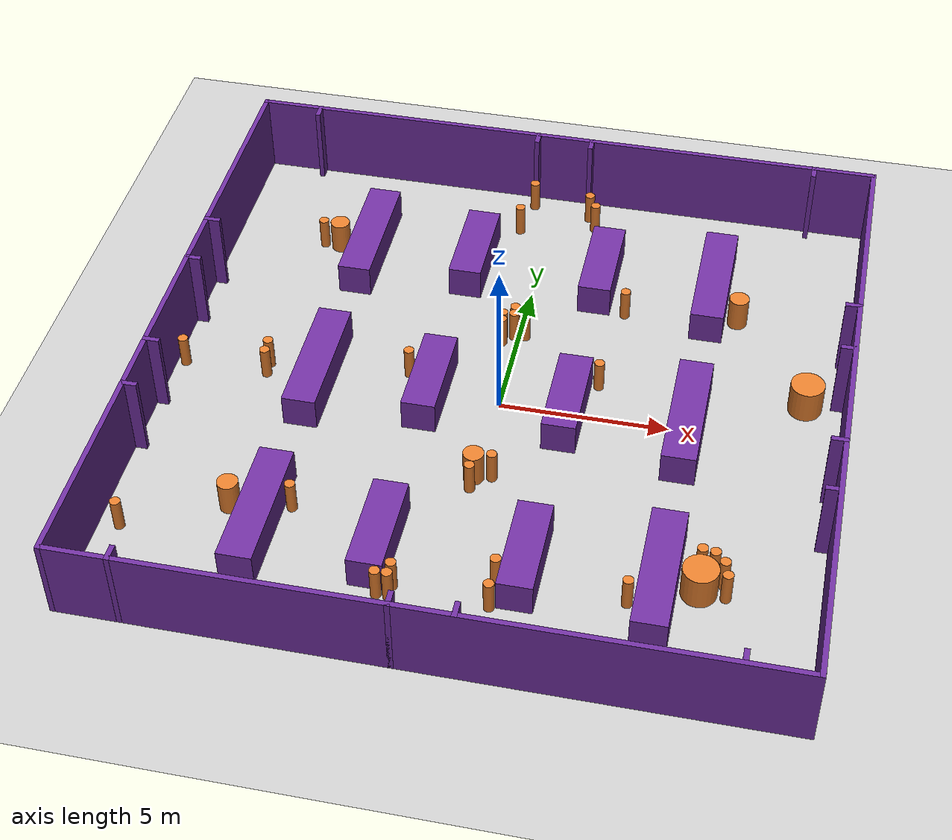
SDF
<sdf version="1.7">
 <world name="default">
  <light name="sun" type="directional">
   <pose>0 0 10 0 -0 0</pose>
   <diffuse>0.8 0.8 0.8 1</diffuse>
   <specular>0.2 0.2 0.2 1</specular>
   <attenuation>
    <range>1000</range>
    <constant>0.9</constant>
    <linear>0.01</linear>
    <quadratic>0.001</quadratic>
   </attenuation>
   <direction>-0.5 0.1 -0.9</direction>
   <spot><inner_angle>0</inner_angle><outer_angle>0</outer_angle><falloff>0</falloff></spot>
  </light>
  <model name="ground_plane">
   <static>1</static>
   <link name="link">
    <collision name="collision">
     <geometry><plane><normal>0 0 1</normal><size>100 100</size></plane></geometry>
     <surface>
      <contact><collide_bitmask>65535</collide_bitmask></contact>
      <friction><ode><mu>100</mu><mu2>50</mu2></ode></friction>
     </surface>
    </collision>
    <visual name="visual">
     <cast_shadows>0</cast_shadows>
     <geometry><plane><normal>0 0 1</normal><size>100 100</size></plane></geometry>
     <material>
      <script><uri>file://media/materials/scripts/gazebo.material</uri><name>Gazebo/Grey</name></script>
     </material>
    </visual>
   </link>
  </model>
  <gravity>0 0 -9.8</gravity>
  <magnetic_field>6e-06 2.3e-05 -4.2e-05</magnetic_field>
  <atmosphere type="adiabatic"/>
  <physics type="ode">
   <max_step_size>0.002</max_step_size>
   <real_time_update_rate>500</real_time_update_rate>
  </physics>
  <scene><ambient>0.4 0.4 0.4 1</ambient><background>0.7 0.7 0.7 1</background><shadows>1</shadows></scene>
  <spherical_coordinates>
   <surface_model>EARTH_WGS84</surface_model>
   <latitude_deg>0</latitude_deg>
   <longitude_deg>0</longitude_deg>
   <elevation>0</elevation>
   <heading_deg>0</heading_deg>
  </spherical_coordinates>
  <model name="B_1_4_0">
   <link name="link_0">
    <inertial>
     <mass>40</mass>
     <inertia><ixx>56.6667</ixx><ixy>0</ixy><ixz>0</ixz><iyy>6.66667</iyy><iyz>0</iyz><izz>56.6667</izz></inertia>
    </inertial>
    <visual name="visual">
     <geometry><box><size>1 4 1</size></box></geometry>
     <material>
      <lighting>1</lighting>
      <script><uri>file://media/materials/scripts/gazebo.material</uri><name>Gazebo/Grey</name></script>
      <shader type="pixel"><normal_map>__default__</normal_map></shader>
      <ambient>0.44 0.19 0.63 1</ambient>
      <diffuse>0.7 0.7 0.7 1</diffuse>
      <specular>0.01 0.01 0.01 1</specular>
      <emissive>0 0 0 1</emissive>
     </material>
    </visual>
    <collision name="collision">
     <geometry><box><size>1 4 1</size></box></geometry>
     <surface>
      <friction>
       <ode><mu>1</mu><mu2>1</mu2><fdir1>0 0 0</fdir1><slip1>0</slip1><slip2>0</slip2></ode>
       <torsional>
        <coefficient>1</coefficient>
        <patch_radius>0</patch_radius>
        <surface_radius>0</surface_radius>
        <use_patch_radius>1</use_patch_radius>
        <ode><slip>0</slip></ode>
       </torsional>
      </friction>
      <bounce><restitution_coefficient>0</restitution_coefficient><threshold>1e+06</threshold></bounce>
      <contact>
       <collide_without_contact>0</collide_without_contact>
       <collide_without_contact_bitmask>1</collide_without_contact_bitmask>
       <collide_bitmask>1</collide_bitmask>
       <ode>
        <soft_cfm>0</soft_cfm>
        <soft_erp>0.2</soft_erp>
        <kp>1e+13</kp>
        <kd>1</kd>
        <max_vel>0.01</max_vel>
        <min_depth>0</min_depth>
       </ode>
       <bullet>
        <split_impulse>1</split_impulse>
        <split_impulse_penetration_threshold>-0.01</split_impulse_penetration_threshold>
        <soft_cfm>0</soft_cfm>
        <soft_erp>0.2</soft_erp>
        <kp>1e+13</kp>
        <kd>1</kd>
       </bullet>
      </contact>
     </surface>
    </collision>
   </link>
   <static>0</static>
   <pose>-5.4852 0.015964 0.5 0 -0 0</pose>
  </model>
  <model name="B_1_4_5">
   <link name="link_0">
    <inertial>
     <mass>40</mass>
     <inertia><ixx>56.6667</ixx><ixy>0</ixy><ixz>0</ixz><iyy>6.66667</iyy><iyz>0</iyz><izz>56.6667</izz></inertia>
    </inertial>
    <visual name="visual">
     <geometry><box><size>1 4 1</size></box></geometry>
     <material>
      <lighting>1</lighting>
      <script><uri>file://media/materials/scripts/gazebo.material</uri><name>Gazebo/Grey</name></script>
      <shader type="pixel"><normal_map>__default__</normal_map></shader>
      <ambient>0.44 0.19 0.63 1</ambient>
      <diffuse>0.7 0.7 0.7 1</diffuse>
      <specular>0.01 0.01 0.01 1</specular>
      <emissive>0 0 0 1</emissive>
     </material>
    </visual>
    <collision name="collision">
     <geometry><box><size>1 4 1</size></box></geometry>
     <surface>
      <friction>
       <ode><mu>1</mu><mu2>1</mu2><fdir1>0 0 0</fdir1><slip1>0</slip1><slip2>0</slip2></ode>
       <torsional>
        <coefficient>1</coefficient>
        <patch_radius>0</patch_radius>
        <surface_radius>0</surface_radius>
        <use_patch_radius>1</use_patch_radius>
        <ode><slip>0</slip></ode>
       </torsional>
      </friction>
      <bounce><restitution_coefficient>0</restitution_coefficient><threshold>1e+06</threshold></bounce>
      <contact>
       <collide_without_contact>0</collide_without_contact>
       <collide_without_contact_bitmask>1</collide_without_contact_bitmask>
       <collide_bitmask>1</collide_bitmask>
       <ode>
        <soft_cfm>0</soft_cfm>
        <soft_erp>0.2</soft_erp>
        <kp>1e+13</kp>
        <kd>1</kd>
        <max_vel>0.01</max_vel>
        <min_depth>0</min_depth>
       </ode>
       <bullet>
        <split_impulse>1</split_impulse>
        <split_impulse_penetration_threshold>-0.01</split_impulse_penetration_threshold>
        <soft_cfm>0</soft_cfm>
        <soft_erp>0.2</soft_erp>
        <kp>1e+13</kp>
        <kd>1</kd>
       </bullet>
      </contact>
     </surface>
    </collision>
   </link>
   <static>0</static>
   <pose>-5.44605 6.01143 0.5 0 -0 0</pose>
  </model>
  <model name="B_1_4_1">
   <link name="link_0">
    <inertial>
     <mass>40</mass>
     <inertia><ixx>56.6667</ixx><ixy>0</ixy><ixz>0</ixz><iyy>6.66667</iyy><iyz>0</iyz><izz>56.6667</izz></inertia>
    </inertial>
    <visual name="visual">
     <geometry><box><size>1 4 1</size></box></geometry>
     <material>
      <lighting>1</lighting>
      <script><uri>file://media/materials/scripts/gazebo.material</uri><name>Gazebo/Grey</name></script>
      <shader type="pixel"><normal_map>__default__</normal_map></shader>
      <ambient>0.44 0.19 0.63 1</ambient>
      <diffuse>0.7 0.7 0.7 1</diffuse>
      <specular>0.01 0.01 0.01 1</specular>
      <emissive>0 0 0 1</emissive>
     </material>
    </visual>
    <collision name="collision">
     <geometry><box><size>1 4 1</size></box></geometry>
     <surface>
      <friction>
       <ode><mu>1</mu><mu2>1</mu2><fdir1>0 0 0</fdir1><slip1>0</slip1><slip2>0</slip2></ode>
       <torsional>
        <coefficient>1</coefficient>
        <patch_radius>0</patch_radius>
        <surface_radius>0</surface_radius>
        <use_patch_radius>1</use_patch_radius>
        <ode><slip>0</slip></ode>
       </torsional>
      </friction>
      <bounce><restitution_coefficient>0</restitution_coefficient><threshold>1e+06</threshold></bounce>
      <contact>
       <collide_without_contact>0</collide_without_contact>
       <collide_without_contact_bitmask>1</collide_without_contact_bitmask>
       <collide_bitmask>1</collide_bitmask>
       <ode>
        <soft_cfm>0</soft_cfm>
        <soft_erp>0.2</soft_erp>
        <kp>1e+13</kp>
        <kd>1</kd>
        <max_vel>0.01</max_vel>
        <min_depth>0</min_depth>
       </ode>
       <bullet>
        <split_impulse>1</split_impulse>
        <split_impulse_penetration_threshold>-0.01</split_impulse_penetration_threshold>
        <soft_cfm>0</soft_cfm>
        <soft_erp>0.2</soft_erp>
        <kp>1e+13</kp>
        <kd>1</kd>
       </bullet>
      </contact>
     </surface>
    </collision>
   </link>
   <static>0</static>
   <pose>-5.50992 -5.97184 0.5 0 -0 0</pose>
  </model>
  <model name="B_1_4_2">
   <link name="link_0">
    <inertial>
     <mass>40</mass>
     <inertia><ixx>56.6667</ixx><ixy>0</ixy><ixz>0</ixz><iyy>6.66667</iyy><iyz>0</iyz><izz>56.6667</izz></inertia>
    </inertial>
    <visual name="visual">
     <geometry><box><size>1 4 1</size></box></geometry>
     <material>
      <lighting>1</lighting>
      <script><uri>file://media/materials/scripts/gazebo.material</uri><name>Gazebo/Grey</name></script>
      <shader type="pixel"><normal_map>__default__</normal_map></shader>
      <ambient>0.44 0.19 0.63 1</ambient>
      <diffuse>0.7 0.7 0.7 1</diffuse>
      <specular>0.01 0.01 0.01 1</specular>
      <emissive>0 0 0 1</emissive>
     </material>
    </visual>
    <collision name="collision">
     <geometry><box><size>1 4 1</size></box></geometry>
     <surface>
      <friction>
       <ode><mu>1</mu><mu2>1</mu2><fdir1>0 0 0</fdir1><slip1>0</slip1><slip2>0</slip2></ode>
       <torsional>
        <coefficient>1</coefficient>
        <patch_radius>0</patch_radius>
        <surface_radius>0</surface_radius>
        <use_patch_radius>1</use_patch_radius>
        <ode><slip>0</slip></ode>
       </torsional>
      </friction>
      <bounce><restitution_coefficient>0</restitution_coefficient><threshold>1e+06</threshold></bounce>
      <contact>
       <collide_without_contact>0</collide_without_contact>
       <collide_without_contact_bitmask>1</collide_without_contact_bitmask>
       <collide_bitmask>1</collide_bitmask>
       <ode>
        <soft_cfm>0</soft_cfm>
        <soft_erp>0.2</soft_erp>
        <kp>1e+13</kp>
        <kd>1</kd>
        <max_vel>0.01</max_vel>
        <min_depth>0</min_depth>
       </ode>
       <bullet>
        <split_impulse>1</split_impulse>
        <split_impulse_penetration_threshold>-0.01</split_impulse_penetration_threshold>
        <soft_cfm>0</soft_cfm>
        <soft_erp>0.2</soft_erp>
        <kp>1e+13</kp>
        <kd>1</kd>
       </bullet>
      </contact>
     </surface>
    </collision>
   </link>
   <static>0</static>
   <pose>5.52612 6.00951 0.5 0 -0 0</pose>
  </model>
  <model name="B_1_4_3">
   <link name="link_0">
    <inertial>
     <mass>40</mass>
     <inertia><ixx>56.6667</ixx><ixy>0</ixy><ixz>0</ixz><iyy>6.66667</iyy><iyz>0</iyz><izz>56.6667</izz></inertia>
    </inertial>
    <visual name="visual">
     <geometry><box><size>1 4 1</size></box></geometry>
     <material>
      <lighting>1</lighting>
      <script><uri>file://media/materials/scripts/gazebo.material</uri><name>Gazebo/Grey</name></script>
      <shader type="pixel"><normal_map>__default__</normal_map></shader>
      <ambient>0.44 0.19 0.63 1</ambient>
      <diffuse>0.7 0.7 0.7 1</diffuse>
      <specular>0.01 0.01 0.01 1</specular>
      <emissive>0 0 0 1</emissive>
     </material>
    </visual>
    <collision name="collision">
     <geometry><box><size>1 4 1</size></box></geometry>
     <surface>
      <friction>
       <ode><mu>1</mu><mu2>1</mu2><fdir1>0 0 0</fdir1><slip1>0</slip1><slip2>0</slip2></ode>
       <torsional>
        <coefficient>1</coefficient>
        <patch_radius>0</patch_radius>
        <surface_radius>0</surface_radius>
        <use_patch_radius>1</use_patch_radius>
        <ode><slip>0</slip></ode>
       </torsional>
      </friction>
      <bounce><restitution_coefficient>0</restitution_coefficient><threshold>1e+06</threshold></bounce>
      <contact>
       <collide_without_contact>0</collide_without_contact>
       <collide_without_contact_bitmask>1</collide_without_contact_bitmask>
       <collide_bitmask>1</collide_bitmask>
       <ode>
        <soft_cfm>0</soft_cfm>
        <soft_erp>0.2</soft_erp>
        <kp>1e+13</kp>
        <kd>1</kd>
        <max_vel>0.01</max_vel>
        <min_depth>0</min_depth>
       </ode>
       <bullet>
        <split_impulse>1</split_impulse>
        <split_impulse_penetration_threshold>-0.01</split_impulse_penetration_threshold>
        <soft_cfm>0</soft_cfm>
        <soft_erp>0.2</soft_erp>
        <kp>1e+13</kp>
        <kd>1</kd>
       </bullet>
      </contact>
     </surface>
    </collision>
   </link>
   <static>0</static>
   <pose>5.49347 -0.022705 0.5 0 -0 0</pose>
  </model>
  <model name="B_1_4_4">
   <link name="link_0">
    <inertial>
     <mass>40</mass>
     <inertia><ixx>56.6667</ixx><ixy>0</ixy><ixz>0</ixz><iyy>6.66667</iyy><iyz>0</iyz><izz>56.6667</izz></inertia>
    </inertial>
    <visual name="visual">
     <geometry><box><size>1 4 1</size></box></geometry>
     <material>
      <lighting>1</lighting>
      <script><uri>file://media/materials/scripts/gazebo.material</uri><name>Gazebo/Grey</name></script>
      <shader type="pixel"><normal_map>__default__</normal_map></shader>
      <ambient>0.44 0.19 0.63 1</ambient>
      <diffuse>0.7 0.7 0.7 1</diffuse>
      <specular>0.01 0.01 0.01 1</specular>
      <emissive>0 0 0 1</emissive>
     </material>
    </visual>
    <collision name="collision">
     <geometry><box><size>1 4 1</size></box></geometry>
     <surface>
      <friction>
       <ode><mu>1</mu><mu2>1</mu2><fdir1>0 0 0</fdir1><slip1>0</slip1><slip2>0</slip2></ode>
       <torsional>
        <coefficient>1</coefficient>
        <patch_radius>0</patch_radius>
        <surface_radius>0</surface_radius>
        <use_patch_radius>1</use_patch_radius>
        <ode><slip>0</slip></ode>
       </torsional>
      </friction>
      <bounce><restitution_coefficient>0</restitution_coefficient><threshold>1e+06</threshold></bounce>
      <contact>
       <collide_without_contact>0</collide_without_contact>
       <collide_without_contact_bitmask>1</collide_without_contact_bitmask>
       <collide_bitmask>1</collide_bitmask>
       <ode>
        <soft_cfm>0</soft_cfm>
        <soft_erp>0.2</soft_erp>
        <kp>1e+13</kp>
        <kd>1</kd>
        <max_vel>0.01</max_vel>
        <min_depth>0</min_depth>
       </ode>
       <bullet>
        <split_impulse>1</split_impulse>
        <split_impulse_penetration_threshold>-0.01</split_impulse_penetration_threshold>
        <soft_cfm>0</soft_cfm>
        <soft_erp>0.2</soft_erp>
        <kp>1e+13</kp>
        <kd>1</kd>
       </bullet>
      </contact>
     </surface>
    </collision>
   </link>
   <static>0</static>
   <pose>5.54818 -5.98559 0.5 0 -0 0</pose>
  </model>
  <model name="B_1_3_0">
   <link name="link_1">
    <inertial>
     <mass>30</mass>
     <inertia><ixx>25</ixx><ixy>0</ixy><ixz>0</ixz><iyy>5</iyy><iyz>0</iyz><izz>25</izz></inertia>
    </inertial>
    <visual name="visual">
     <geometry><box><size>1 3 1</size></box></geometry>
     <material>
      <lighting>1</lighting>
      <script><uri>file://media/materials/scripts/gazebo.material</uri><name>Gazebo/Grey</name></script>
      <shader type="pixel"><normal_map>__default__</normal_map></shader>
      <ambient>0.44 0.19 0.63 1</ambient>
      <diffuse>0.7 0.7 0.7 1</diffuse>
      <specular>0.01 0.01 0.01 1</specular>
      <emissive>0 0 0 1</emissive>
     </material>
    </visual>
    <collision name="collision">
     <geometry><box><size>1 3 1</size></box></geometry>
     <surface>
      <friction>
       <ode><mu>1</mu><mu2>1</mu2><fdir1>0 0 0</fdir1><slip1>0</slip1><slip2>0</slip2></ode>
       <torsional>
        <coefficient>1</coefficient>
        <patch_radius>0</patch_radius>
        <surface_radius>0</surface_radius>
        <use_patch_radius>1</use_patch_radius>
        <ode><slip>0</slip></ode>
       </torsional>
      </friction>
      <bounce><restitution_coefficient>0</restitution_coefficient><threshold>1e+06</threshold></bounce>
      <contact>
       <collide_without_contact>0</collide_without_contact>
       <collide_without_contact_bitmask>1</collide_without_contact_bitmask>
       <collide_bitmask>1</collide_bitmask>
       <ode>
        <soft_cfm>0</soft_cfm>
        <soft_erp>0.2</soft_erp>
        <kp>1e+13</kp>
        <kd>1</kd>
        <max_vel>0.01</max_vel>
        <min_depth>0</min_depth>
       </ode>
       <bullet>
        <split_impulse>1</split_impulse>
        <split_impulse_penetration_threshold>-0.01</split_impulse_penetration_threshold>
        <soft_cfm>0</soft_cfm>
        <soft_erp>0.2</soft_erp>
        <kp>1e+13</kp>
        <kd>1</kd>
       </bullet>
      </contact>
     </surface>
    </collision>
   </link>
   <static>0</static>
   <pose>1.99632 6.07045 0.5 0 -0 0</pose>
  </model>
  <model name="B_1_3_1">
   <link name="link_1">
    <inertial>
     <mass>30</mass>
     <inertia><ixx>25</ixx><ixy>0</ixy><ixz>0</ixz><iyy>5</iyy><iyz>0</iyz><izz>25</izz></inertia>
    </inertial>
    <visual name="visual">
     <geometry><box><size>1 3 1</size></box></geometry>
     <material>
      <lighting>1</lighting>
      <script><uri>file://media/materials/scripts/gazebo.material</uri><name>Gazebo/Grey</name></script>
      <shader type="pixel"><normal_map>__default__</normal_map></shader>
      <ambient>0.44 0.19 0.63 1</ambient>
      <diffuse>0.7 0.7 0.7 1</diffuse>
      <specular>0.01 0.01 0.01 1</specular>
      <emissive>0 0 0 1</emissive>
     </material>
    </visual>
    <collision name="collision">
     <geometry><box><size>1 3 1</size></box></geometry>
     <surface>
      <friction>
       <ode><mu>1</mu><mu2>1</mu2><fdir1>0 0 0</fdir1><slip1>0</slip1><slip2>0</slip2></ode>
       <torsional>
        <coefficient>1</coefficient>
        <patch_radius>0</patch_radius>
        <surface_radius>0</surface_radius>
        <use_patch_radius>1</use_patch_radius>
        <ode><slip>0</slip></ode>
       </torsional>
      </friction>
      <bounce><restitution_coefficient>0</restitution_coefficient><threshold>1e+06</threshold></bounce>
      <contact>
       <collide_without_contact>0</collide_without_contact>
       <collide_without_contact_bitmask>1</collide_without_contact_bitmask>
       <collide_bitmask>1</collide_bitmask>
       <ode>
        <soft_cfm>0</soft_cfm>
        <soft_erp>0.2</soft_erp>
        <kp>1e+13</kp>
        <kd>1</kd>
        <max_vel>0.01</max_vel>
        <min_depth>0</min_depth>
       </ode>
       <bullet>
        <split_impulse>1</split_impulse>
        <split_impulse_penetration_threshold>-0.01</split_impulse_penetration_threshold>
        <soft_cfm>0</soft_cfm>
        <soft_erp>0.2</soft_erp>
        <kp>1e+13</kp>
        <kd>1</kd>
       </bullet>
      </contact>
     </surface>
    </collision>
   </link>
   <static>0</static>
   <pose>-2.0578 6.06122 0.5 0 -0 0</pose>
  </model>
  <model name="B_1_3_2">
   <link name="link_1">
    <inertial>
     <mass>30</mass>
     <inertia><ixx>25</ixx><ixy>0</ixy><ixz>0</ixz><iyy>5</iyy><iyz>0</iyz><izz>25</izz></inertia>
    </inertial>
    <visual name="visual">
     <geometry><box><size>1 3 1</size></box></geometry>
     <material>
      <lighting>1</lighting>
      <script><uri>file://media/materials/scripts/gazebo.material</uri><name>Gazebo/Grey</name></script>
      <shader type="pixel"><normal_map>__default__</normal_map></shader>
      <ambient>0.44 0.19 0.63 1</ambient>
      <diffuse>0.7 0.7 0.7 1</diffuse>
      <specular>0.01 0.01 0.01 1</specular>
      <emissive>0 0 0 1</emissive>
     </material>
    </visual>
    <collision name="collision">
     <geometry><box><size>1 3 1</size></box></geometry>
     <surface>
      <friction>
       <ode><mu>1</mu><mu2>1</mu2><fdir1>0 0 0</fdir1><slip1>0</slip1><slip2>0</slip2></ode>
       <torsional>
        <coefficient>1</coefficient>
        <patch_radius>0</patch_radius>
        <surface_radius>0</surface_radius>
        <use_patch_radius>1</use_patch_radius>
        <ode><slip>0</slip></ode>
       </torsional>
      </friction>
      <bounce><restitution_coefficient>0</restitution_coefficient><threshold>1e+06</threshold></bounce>
      <contact>
       <collide_without_contact>0</collide_without_contact>
       <collide_without_contact_bitmask>1</collide_without_contact_bitmask>
       <collide_bitmask>1</collide_bitmask>
       <ode>
        <soft_cfm>0</soft_cfm>
        <soft_erp>0.2</soft_erp>
        <kp>1e+13</kp>
        <kd>1</kd>
        <max_vel>0.01</max_vel>
        <min_depth>0</min_depth>
       </ode>
       <bullet>
        <split_impulse>1</split_impulse>
        <split_impulse_penetration_threshold>-0.01</split_impulse_penetration_threshold>
        <soft_cfm>0</soft_cfm>
        <soft_erp>0.2</soft_erp>
        <kp>1e+13</kp>
        <kd>1</kd>
       </bullet>
      </contact>
     </surface>
    </collision>
   </link>
   <static>0</static>
   <pose>-2.09356 0.051228 0.5 0 -0 0</pose>
  </model>
  <model name="B_1_3_3">
   <link name="link_1">
    <inertial>
     <mass>30</mass>
     <inertia><ixx>25</ixx><ixy>0</ixy><ixz>0</ixz><iyy>5</iyy><iyz>0</iyz><izz>25</izz></inertia>
    </inertial>
    <visual name="visual">
     <geometry><box><size>1 3 1</size></box></geometry>
     <material>
      <lighting>1</lighting>
      <script><uri>file://media/materials/scripts/gazebo.material</uri><name>Gazebo/Grey</name></script>
      <shader type="pixel"><normal_map>__default__</normal_map></shader>
      <ambient>0.44 0.19 0.63 1</ambient>
      <diffuse>0.7 0.7 0.7 1</diffuse>
      <specular>0.01 0.01 0.01 1</specular>
      <emissive>0 0 0 1</emissive>
     </material>
    </visual>
    <collision name="collision">
     <geometry><box><size>1 3 1</size></box></geometry>
     <surface>
      <friction>
       <ode><mu>1</mu><mu2>1</mu2><fdir1>0 0 0</fdir1><slip1>0</slip1><slip2>0</slip2></ode>
       <torsional>
        <coefficient>1</coefficient>
        <patch_radius>0</patch_radius>
        <surface_radius>0</surface_radius>
        <use_patch_radius>1</use_patch_radius>
        <ode><slip>0</slip></ode>
       </torsional>
      </friction>
      <bounce><restitution_coefficient>0</restitution_coefficient><threshold>1e+06</threshold></bounce>
      <contact>
       <collide_without_contact>0</collide_without_contact>
       <collide_without_contact_bitmask>1</collide_without_contact_bitmask>
       <collide_bitmask>1</collide_bitmask>
       <ode>
        <soft_cfm>0</soft_cfm>
        <soft_erp>0.2</soft_erp>
        <kp>1e+13</kp>
        <kd>1</kd>
        <max_vel>0.01</max_vel>
        <min_depth>0</min_depth>
       </ode>
       <bullet>
        <split_impulse>1</split_impulse>
        <split_impulse_penetration_threshold>-0.01</split_impulse_penetration_threshold>
        <soft_cfm>0</soft_cfm>
        <soft_erp>0.2</soft_erp>
        <kp>1e+13</kp>
        <kd>1</kd>
       </bullet>
      </contact>
     </surface>
    </collision>
   </link>
   <static>0</static>
   <pose>1.99973 0.020044 0.5 0 -0 0</pose>
  </model>
  <model name="B_1_3_5">
   <link name="link_1">
    <inertial>
     <mass>30</mass>
     <inertia><ixx>25</ixx><ixy>0</ixy><ixz>0</ixz><iyy>5</iyy><iyz>0</iyz><izz>25</izz></inertia>
    </inertial>
    <visual name="visual">
     <geometry><box><size>1 3 1</size></box></geometry>
     <material>
      <lighting>1</lighting>
      <script><uri>file://media/materials/scripts/gazebo.material</uri><name>Gazebo/Grey</name></script>
      <shader type="pixel"><normal_map>__default__</normal_map></shader>
      <ambient>0.44 0.19 0.63 1</ambient>
      <diffuse>0.7 0.7 0.7 1</diffuse>
      <specular>0.01 0.01 0.01 1</specular>
      <emissive>0 0 0 1</emissive>
     </material>
    </visual>
    <collision name="collision">
     <geometry><box><size>1 3 1</size></box></geometry>
     <surface>
      <friction>
       <ode><mu>1</mu><mu2>1</mu2><fdir1>0 0 0</fdir1><slip1>0</slip1><slip2>0</slip2></ode>
       <torsional>
        <coefficient>1</coefficient>
        <patch_radius>0</patch_radius>
        <surface_radius>0</surface_radius>
        <use_patch_radius>1</use_patch_radius>
        <ode><slip>0</slip></ode>
       </torsional>
      </friction>
      <bounce><restitution_coefficient>0</restitution_coefficient><threshold>1e+06</threshold></bounce>
      <contact>
       <collide_without_contact>0</collide_without_contact>
       <collide_without_contact_bitmask>1</collide_without_contact_bitmask>
       <collide_bitmask>1</collide_bitmask>
       <ode>
        <soft_cfm>0</soft_cfm>
        <soft_erp>0.2</soft_erp>
        <kp>1e+13</kp>
        <kd>1</kd>
        <max_vel>0.01</max_vel>
        <min_depth>0</min_depth>
       </ode>
       <bullet>
        <split_impulse>1</split_impulse>
        <split_impulse_penetration_threshold>-0.01</split_impulse_penetration_threshold>
        <soft_cfm>0</soft_cfm>
        <soft_erp>0.2</soft_erp>
        <kp>1e+13</kp>
        <kd>1</kd>
       </bullet>
      </contact>
     </surface>
    </collision>
   </link>
   <static>0</static>
   <pose>1.94317 -5.96793 0.5 0 -0 0</pose>
  </model>
  <model name="B_1_3_4">
   <link name="link_1">
    <inertial>
     <mass>30</mass>
     <inertia><ixx>25</ixx><ixy>0</ixy><ixz>0</ixz><iyy>5</iyy><iyz>0</iyz><izz>25</izz></inertia>
    </inertial>
    <visual name="visual">
     <geometry><box><size>1 3 1</size></box></geometry>
     <material>
      <lighting>1</lighting>
      <script><uri>file://media/materials/scripts/gazebo.material</uri><name>Gazebo/Grey</name></script>
      <shader type="pixel"><normal_map>__default__</normal_map></shader>
      <ambient>0.44 0.19 0.63 1</ambient>
      <diffuse>0.7 0.7 0.7 1</diffuse>
      <specular>0.01 0.01 0.01 1</specular>
      <emissive>0 0 0 1</emissive>
     </material>
    </visual>
    <collision name="collision">
     <geometry><box><size>1 3 1</size></box></geometry>
     <surface>
      <friction>
       <ode><mu>1</mu><mu2>1</mu2><fdir1>0 0 0</fdir1><slip1>0</slip1><slip2>0</slip2></ode>
       <torsional>
        <coefficient>1</coefficient>
        <patch_radius>0</patch_radius>
        <surface_radius>0</surface_radius>
        <use_patch_radius>1</use_patch_radius>
        <ode><slip>0</slip></ode>
       </torsional>
      </friction>
      <bounce><restitution_coefficient>0</restitution_coefficient><threshold>1e+06</threshold></bounce>
      <contact>
       <collide_without_contact>0</collide_without_contact>
       <collide_without_contact_bitmask>1</collide_without_contact_bitmask>
       <collide_bitmask>1</collide_bitmask>
       <ode>
        <soft_cfm>0</soft_cfm>
        <soft_erp>0.2</soft_erp>
        <kp>1e+13</kp>
        <kd>1</kd>
        <max_vel>0.01</max_vel>
        <min_depth>0</min_depth>
       </ode>
       <bullet>
        <split_impulse>1</split_impulse>
        <split_impulse_penetration_threshold>-0.01</split_impulse_penetration_threshold>
        <soft_cfm>0</soft_cfm>
        <soft_erp>0.2</soft_erp>
        <kp>1e+13</kp>
        <kd>1</kd>
       </bullet>
      </contact>
     </surface>
    </collision>
   </link>
   <static>0</static>
   <pose>-2.08937 -5.9974 0.5 0 -0 0</pose>
  </model>
  <model name="shelter_20_20">
   <pose>0.003122 0.05499 0 0 -0 0</pose>
   <link name="Wall_0">
    <collision name="Wall_0_Collision">
     <geometry><box><size>20 0.15 2.5</size></box></geometry>
     <pose>0 0 1.25 0 -0 0</pose>
    </collision>
    <visual name="Wall_0_Visual">
     <pose>0 0 1.25 0 -0 0</pose>
     <geometry><box><size>20 0.15 2.5</size></box></geometry>
     <material>
      <script><uri>file://media/materials/scripts/gazebo.material</uri><name>Gazebo/Grey</name></script>
      <ambient>0.439216 0.188235 0.627451 1</ambient>
     </material>
     <meta><layer>0</layer></meta>
    </visual>
    <pose>-0 9.925 0 0 -0 0</pose>
   </link>
   <link name="Wall_1">
    <collision name="Wall_1_Collision">
     <geometry><box><size>20 0.15 2.5</size></box></geometry>
     <pose>0 0 1.25 0 -0 0</pose>
    </collision>
    <visual name="Wall_1_Visual">
     <pose>0 0 1.25 0 -0 0</pose>
     <geometry><box><size>20 0.15 2.5</size></box></geometry>
     <material>
      <script><uri>file://media/materials/scripts/gazebo.material</uri><name>Gazebo/Grey</name></script>
      <ambient>0.439216 0.188235 0.627451 1</ambient>
     </material>
     <meta><layer>0</layer></meta>
    </visual>
    <pose>9.925 0 0 0 -0 -1.5708</pose>
   </link>
   <link name="Wall_2">
    <collision name="Wall_2_Collision">
     <geometry><box><size>20 0.15 2.5</size></box></geometry>
     <pose>0 0 1.25 0 -0 0</pose>
    </collision>
    <visual name="Wall_2_Visual">
     <pose>0 0 1.25 0 -0 0</pose>
     <geometry><box><size>20 0.15 2.5</size></box></geometry>
     <material>
      <script><uri>file://media/materials/scripts/gazebo.material</uri><name>Gazebo/Grey</name></script>
      <ambient>0.439216 0.188235 0.627451 1</ambient>
     </material>
     <meta><layer>0</layer></meta>
    </visual>
    <pose>-0 -9.925 0 0 -0 3.14159</pose>
   </link>
   <link name="Wall_27">
    <collision name="Wall_27_Collision">
     <geometry><box><size>0.5 0.15 2.5</size></box></geometry>
     <pose>0 0 1.25 0 -0 0</pose>
    </collision>
    <visual name="Wall_27_Visual">
     <pose>0 0 1.25 0 -0 0</pose>
     <geometry><box><size>0.5 0.15 2.5</size></box></geometry>
     <material>
      <script><uri>file://media/materials/scripts/gazebo.material</uri><name>Gazebo/Grey</name></script>
      <ambient>0.439216 0.188235 0.627451 1</ambient>
     </material>
     <meta><layer>0</layer></meta>
    </visual>
    <pose>8.075 -9.75 0 0 -0 1.5708</pose>
   </link>
   <link name="Wall_3">
    <collision name="Wall_3_Collision">
     <geometry><box><size>20 0.15 2.5</size></box></geometry>
     <pose>0 0 1.25 0 -0 0</pose>
    </collision>
    <visual name="Wall_3_Visual">
     <pose>0 0 1.25 0 -0 0</pose>
     <geometry><box><size>20 0.15 2.5</size></box></geometry>
     <material>
      <script><uri>file://media/materials/scripts/gazebo.material</uri><name>Gazebo/Grey</name></script>
      <ambient>0.439216 0.188235 0.627451 1</ambient>
     </material>
     <meta><layer>0</layer></meta>
    </visual>
    <pose>-9.925 0 0 0 -0 1.5708</pose>
   </link>
   <link name="Wall_30">
    <collision name="Wall_30_Collision">
     <geometry><box><size>0.5 0.15 2.5</size></box></geometry>
     <pose>0 0 1.25 0 -0 0</pose>
    </collision>
    <visual name="Wall_30_Visual">
     <pose>0 0 1.25 0 -0 0</pose>
     <geometry><box><size>0.5 0.15 2.5</size></box></geometry>
     <material>
      <script><uri>file://media/materials/scripts/gazebo.material</uri><name>Gazebo/Grey</name></script>
      <ambient>0.439216 0.188235 0.627451 1</ambient>
     </material>
     <meta><layer>0</layer></meta>
    </visual>
    <pose>-8.075 -9.75 0 0 -0 1.5708</pose>
   </link>
   <link name="Wall_33">
    <collision name="Wall_33_Collision">
     <geometry><box><size>0.5 0.15 2.5</size></box></geometry>
     <pose>0 0 1.25 0 -0 0</pose>
    </collision>
    <visual name="Wall_33_Visual">
     <pose>0 0 1.25 0 -0 0</pose>
     <geometry><box><size>0.5 0.15 2.5</size></box></geometry>
     <material>
      <script><uri>file://media/materials/scripts/gazebo.material</uri><name>Gazebo/Grey</name></script>
      <ambient>0.439216 0.188235 0.627451 1</ambient>
     </material>
     <meta><layer>0</layer></meta>
    </visual>
    <pose>-0.775 -9.75 0 0 -0 1.5708</pose>
   </link>
   <link name="Wall_36">
    <collision name="Wall_36_Collision">
     <geometry><box><size>0.5 0.15 2.5</size></box></geometry>
     <pose>0 0 1.25 0 -0 0</pose>
    </collision>
    <visual name="Wall_36_Visual">
     <pose>0 0 1.25 0 -0 0</pose>
     <geometry><box><size>0.5 0.15 2.5</size></box></geometry>
     <material>
      <script><uri>file://media/materials/scripts/gazebo.material</uri><name>Gazebo/Grey</name></script>
      <ambient>0.439216 0.188235 0.627451 1</ambient>
     </material>
     <meta><layer>0</layer></meta>
    </visual>
    <pose>0.925 -9.75 0 0 -0 1.5708</pose>
   </link>
   <link name="Wall_39">
    <collision name="Wall_39_Collision">
     <geometry><box><size>0.5 0.15 2.5</size></box></geometry>
     <pose>0 0 1.25 0 -0 0</pose>
    </collision>
    <visual name="Wall_39_Visual">
     <pose>0 0 1.25 0 -0 0</pose>
     <geometry><box><size>0.5 0.15 2.5</size></box></geometry>
     <material>
      <script><uri>file://media/materials/scripts/gazebo.material</uri><name>Gazebo/Grey</name></script>
      <ambient>0.439216 0.188235 0.627451 1</ambient>
     </material>
     <meta><layer>0</layer></meta>
    </visual>
    <pose>-8.075 9.75 0 0 -0 -1.5708</pose>
   </link>
   <link name="Wall_42">
    <collision name="Wall_42_Collision">
     <geometry><box><size>0.5 0.15 2.5</size></box></geometry>
     <pose>0 0 1.25 0 -0 0</pose>
    </collision>
    <visual name="Wall_42_Visual">
     <pose>0 0 1.25 0 -0 0</pose>
     <geometry><box><size>0.5 0.15 2.5</size></box></geometry>
     <material>
      <script><uri>file://media/materials/scripts/gazebo.material</uri><name>Gazebo/Grey</name></script>
      <ambient>0.439216 0.188235 0.627451 1</ambient>
     </material>
     <meta><layer>0</layer></meta>
    </visual>
    <pose>8.075 9.75 0 0 -0 -1.5708</pose>
   </link>
   <link name="Wall_45">
    <collision name="Wall_45_Collision">
     <geometry><box><size>0.5 0.15 2.5</size></box></geometry>
     <pose>0 0 1.25 0 -0 0</pose>
    </collision>
    <visual name="Wall_45_Visual">
     <pose>0 0 1.25 0 -0 0</pose>
     <geometry><box><size>0.5 0.15 2.5</size></box></geometry>
     <material>
      <script><uri>file://media/materials/scripts/gazebo.material</uri><name>Gazebo/Grey</name></script>
      <ambient>0.439216 0.188235 0.627451 1</ambient>
     </material>
     <meta><layer>0</layer></meta>
    </visual>
    <pose>-0.775 9.75 0 0 -0 -1.5708</pose>
   </link>
   <link name="Wall_51">
    <collision name="Wall_51_Collision">
     <geometry><box><size>0.5 0.15 2.5</size></box></geometry>
     <pose>0 0 1.25 0 -0 0</pose>
    </collision>
    <visual name="Wall_51_Visual">
     <pose>0 0 1.25 0 -0 0</pose>
     <geometry><box><size>0.5 0.15 2.5</size></box></geometry>
     <material>
      <script><uri>file://media/materials/scripts/gazebo.material</uri><name>Gazebo/Grey</name></script>
      <ambient>0.439216 0.188235 0.627451 1</ambient>
     </material>
     <meta><layer>0</layer></meta>
    </visual>
    <pose>0.962943 9.75 0 0 -0 -1.5708</pose>
   </link>
   <link name="Wall_54">
    <collision name="Wall_54_Collision">
     <geometry><box><size>0.5 0.15 2.5</size></box></geometry>
     <pose>0 0 1.25 0 -0 0</pose>
    </collision>
    <visual name="Wall_54_Visual">
     <pose>0 0 1.25 0 -0 0</pose>
     <geometry><box><size>0.5 0.15 2.5</size></box></geometry>
     <material>
      <script><uri>file://media/materials/scripts/gazebo.material</uri><name>Gazebo/Grey</name></script>
      <ambient>0.439216 0.188235 0.627451 1</ambient>
     </material>
     <meta><layer>0</layer></meta>
    </visual>
    <pose>-9.75 1.775 0 0 -0 0</pose>
   </link>
   <link name="Wall_57">
    <collision name="Wall_57_Collision">
     <geometry><box><size>0.5 0.15 2.5</size></box></geometry>
     <pose>0 0 1.25 0 -0 0</pose>
    </collision>
    <visual name="Wall_57_Visual">
     <pose>0 0 1.25 0 -0 0</pose>
     <geometry><box><size>0.5 0.15 2.5</size></box></geometry>
     <material>
      <script><uri>file://media/materials/scripts/gazebo.material</uri><name>Gazebo/Grey</name></script>
      <ambient>0.439216 0.188235 0.627451 1</ambient>
     </material>
     <meta><layer>0</layer></meta>
    </visual>
    <pose>-9.75 3.625 0 0 -0 0</pose>
   </link>
   <link name="Wall_60">
    <collision name="Wall_60_Collision">
     <geometry><box><size>0.5 0.15 2.5</size></box></geometry>
     <pose>0 0 1.25 0 -0 0</pose>
    </collision>
    <visual name="Wall_60_Visual">
     <pose>0 0 1.25 0 -0 0</pose>
     <geometry><box><size>0.5 0.15 2.5</size></box></geometry>
     <material>
      <script><uri>file://media/materials/scripts/gazebo.material</uri><name>Gazebo/Grey</name></script>
      <ambient>0.439216 0.188235 0.627451 1</ambient>
     </material>
     <meta><layer>0</layer></meta>
    </visual>
    <pose>9.75 1.775 0 0 -0 3.14159</pose>
   </link>
   <link name="Wall_63">
    <collision name="Wall_63_Collision">
     <geometry><box><size>0.5 0.15 2.5</size></box></geometry>
     <pose>0 0 1.25 0 -0 0</pose>
    </collision>
    <visual name="Wall_63_Visual">
     <pose>0 0 1.25 0 -0 0</pose>
     <geometry><box><size>0.5 0.15 2.5</size></box></geometry>
     <material>
      <script><uri>file://media/materials/scripts/gazebo.material</uri><name>Gazebo/Grey</name></script>
      <ambient>0.439216 0.188235 0.627451 1</ambient>
     </material>
     <meta><layer>0</layer></meta>
    </visual>
    <pose>9.75 3.625 0 0 -0 3.14159</pose>
   </link>
   <link name="Wall_69">
    <collision name="Wall_69_Collision">
     <geometry><box><size>0.5 0.15 2.5</size></box></geometry>
     <pose>0 0 1.25 0 -0 0</pose>
    </collision>
    <visual name="Wall_69_Visual">
     <pose>0 0 1.25 0 -0 0</pose>
     <geometry><box><size>0.5 0.15 2.5</size></box></geometry>
     <material>
      <script><uri>file://media/materials/scripts/gazebo.material</uri><name>Gazebo/Grey</name></script>
      <ambient>0.439216 0.188235 0.627451 1</ambient>
     </material>
     <meta><layer>0</layer></meta>
    </visual>
    <pose>-9.75 -3.775 0 0 -0 0</pose>
   </link>
   <link name="Wall_83">
    <collision name="Wall_83_Collision">
     <geometry><box><size>0.5 0.15 2.5</size></box></geometry>
     <pose>0 0 1.25 0 -0 0</pose>
    </collision>
    <visual name="Wall_83_Visual">
     <pose>0 0 1.25 0 -0 0</pose>
     <geometry><box><size>0.5 0.15 2.5</size></box></geometry>
     <material>
      <script><uri>file://media/materials/scripts/gazebo.material</uri><name>Gazebo/Grey</name></script>
      <ambient>0.439216 0.188235 0.627451 1</ambient>
     </material>
     <meta><layer>0</layer></meta>
    </visual>
    <pose>-9.75 -1.925 0 0 -0 0</pose>
   </link>
   <link name="Wall_88">
    <collision name="Wall_88_Collision">
     <geometry><box><size>0.5 0.15 2.5</size></box></geometry>
     <pose>0 0 1.25 0 -0 0</pose>
    </collision>
    <visual name="Wall_88_Visual">
     <pose>0 0 1.25 0 -0 0</pose>
     <geometry><box><size>0.5 0.15 2.5</size></box></geometry>
     <material>
      <script><uri>file://media/materials/scripts/gazebo.material</uri><name>Gazebo/Grey</name></script>
      <ambient>0.439216 0.188235 0.627451 1</ambient>
     </material>
     <meta><layer>0</layer></meta>
    </visual>
    <pose>9.75 -1.925 0 0 -0 3.14159</pose>
   </link>
   <link name="Wall_90">
    <collision name="Wall_90_Collision">
     <geometry><box><size>0.5 0.15 2.5</size></box></geometry>
     <pose>0 0 1.25 0 -0 0</pose>
    </collision>
    <visual name="Wall_90_Visual">
     <pose>0 0 1.25 0 -0 0</pose>
     <geometry><box><size>0.5 0.15 2.5</size></box></geometry>
     <material>
      <script><uri>file://media/materials/scripts/gazebo.material</uri><name>Gazebo/Grey</name></script>
      <ambient>0.439216 0.188235 0.627451 1</ambient>
     </material>
     <meta><layer>0</layer></meta>
    </visual>
    <pose>9.75 -3.775 0 0 -0 0</pose>
   </link>
   <static>1</static>
  </model>
  <model name="C_03">
   <link name="link_3">
    <inertial>
     <mass>2.82743</mass>
     <inertia>
      <ixx>0.299237</ixx>
      <ixy>0</ixy>
      <ixz>0</ixz>
      <iyy>0.299237</iyy>
      <iyz>0</iyz>
      <izz>0.127235</izz>
     </inertia>
    </inertial>
    <visual name="visual">
     <geometry><cylinder><radius>0.15</radius><length>1</length></cylinder></geometry>
     <material>
      <lighting>1</lighting>
      <script><uri>file://media/materials/scripts/gazebo.material</uri><name>Gazebo/Grey</name></script>
      <shader type="pixel"><normal_map>__default__</normal_map></shader>
      <ambient>0.9 0.5 0.18 1</ambient>
      <diffuse>0.7 0.7 0.7 1</diffuse>
      <specular>0.01 0.01 0.01 1</specular>
      <emissive>0 0 0 1</emissive>
     </material>
    </visual>
    <collision name="collision">
     <geometry><cylinder><radius>0.15</radius><length>1</length></cylinder></geometry>
     <surface>
      <friction>
       <ode><mu>1</mu><mu2>1</mu2><fdir1>0 0 0</fdir1><slip1>0</slip1><slip2>0</slip2></ode>
       <torsional>
        <coefficient>1</coefficient>
        <patch_radius>0</patch_radius>
        <surface_radius>0</surface_radius>
        <use_patch_radius>1</use_patch_radius>
        <ode><slip>0</slip></ode>
       </torsional>
      </friction>
      <bounce><restitution_coefficient>0</restitution_coefficient><threshold>1e+06</threshold></bounce>
      <contact>
       <collide_without_contact>0</collide_without_contact>
       <collide_without_contact_bitmask>1</collide_without_contact_bitmask>
       <collide_bitmask>1</collide_bitmask>
       <ode>
        <soft_cfm>0</soft_cfm>
        <soft_erp>0.2</soft_erp>
        <kp>1e+13</kp>
        <kd>1</kd>
        <max_vel>0.01</max_vel>
        <min_depth>0</min_depth>
       </ode>
       <bullet>
        <split_impulse>1</split_impulse>
        <split_impulse_penetration_threshold>-0.01</split_impulse_penetration_threshold>
        <soft_cfm>0</soft_cfm>
        <soft_erp>0.2</soft_erp>
        <kp>1e+13</kp>
        <kd>1</kd>
       </bullet>
      </contact>
     </surface>
    </collision>
   </link>
   <static>0</static>
   <pose>-0.508974 2.95827 0.499805 0 -0 6.7e-05</pose>
  </model>
  <model name="C_03_0">
   <link name="link_3">
    <inertial>
     <mass>2.82743</mass>
     <inertia>
      <ixx>0.299237</ixx>
      <ixy>0</ixy>
      <ixz>0</ixz>
      <iyy>0.299237</iyy>
      <iyz>0</iyz>
      <izz>0.127235</izz>
     </inertia>
    </inertial>
    <visual name="visual">
     <geometry><cylinder><radius>0.15</radius><length>1</length></cylinder></geometry>
     <material>
      <lighting>1</lighting>
      <script><uri>file://media/materials/scripts/gazebo.material</uri><name>Gazebo/Grey</name></script>
      <shader type="pixel"><normal_map>__default__</normal_map></shader>
      <ambient>0.9 0.5 0.18 1</ambient>
      <diffuse>0.7 0.7 0.7 1</diffuse>
      <specular>0.01 0.01 0.01 1</specular>
      <emissive>0 0 0 1</emissive>
     </material>
    </visual>
    <collision name="collision">
     <geometry><cylinder><radius>0.15</radius><length>1</length></cylinder></geometry>
     <surface>
      <friction>
       <ode><mu>1</mu><mu2>1</mu2><fdir1>0 0 0</fdir1><slip1>0</slip1><slip2>0</slip2></ode>
       <torsional>
        <coefficient>1</coefficient>
        <patch_radius>0</patch_radius>
        <surface_radius>0</surface_radius>
        <use_patch_radius>1</use_patch_radius>
        <ode><slip>0</slip></ode>
       </torsional>
      </friction>
      <bounce><restitution_coefficient>0</restitution_coefficient><threshold>1e+06</threshold></bounce>
      <contact>
       <collide_without_contact>0</collide_without_contact>
       <collide_without_contact_bitmask>1</collide_without_contact_bitmask>
       <collide_bitmask>1</collide_bitmask>
       <ode>
        <soft_cfm>0</soft_cfm>
        <soft_erp>0.2</soft_erp>
        <kp>1e+13</kp>
        <kd>1</kd>
        <max_vel>0.01</max_vel>
        <min_depth>0</min_depth>
       </ode>
       <bullet>
        <split_impulse>1</split_impulse>
        <split_impulse_penetration_threshold>-0.01</split_impulse_penetration_threshold>
        <soft_cfm>0</soft_cfm>
        <soft_erp>0.2</soft_erp>
        <kp>1e+13</kp>
        <kd>1</kd>
       </bullet>
      </contact>
     </surface>
    </collision>
   </link>
   <static>0</static>
   <pose>-0.163929 2.98337 0.499805 0 -0 6.5e-05</pose>
  </model>
  <model name="C_03_1">
   <link name="link_3">
    <inertial>
     <mass>2.82743</mass>
     <inertia>
      <ixx>0.299237</ixx>
      <ixy>0</ixy>
      <ixz>0</ixz>
      <iyy>0.299237</iyy>
      <iyz>0</iyz>
      <izz>0.127235</izz>
     </inertia>
    </inertial>
    <visual name="visual">
     <geometry><cylinder><radius>0.15</radius><length>1</length></cylinder></geometry>
     <material>
      <lighting>1</lighting>
      <script><uri>file://media/materials/scripts/gazebo.material</uri><name>Gazebo/Grey</name></script>
      <shader type="pixel"><normal_map>__default__</normal_map></shader>
      <ambient>0.9 0.5 0.18 1</ambient>
      <diffuse>0.7 0.7 0.7 1</diffuse>
      <specular>0.01 0.01 0.01 1</specular>
      <emissive>0 0 0 1</emissive>
     </material>
    </visual>
    <collision name="collision">
     <geometry><cylinder><radius>0.15</radius><length>1</length></cylinder></geometry>
     <surface>
      <friction>
       <ode><mu>1</mu><mu2>1</mu2><fdir1>0 0 0</fdir1><slip1>0</slip1><slip2>0</slip2></ode>
       <torsional>
        <coefficient>1</coefficient>
        <patch_radius>0</patch_radius>
        <surface_radius>0</surface_radius>
        <use_patch_radius>1</use_patch_radius>
        <ode><slip>0</slip></ode>
       </torsional>
      </friction>
      <bounce><restitution_coefficient>0</restitution_coefficient><threshold>1e+06</threshold></bounce>
      <contact>
       <collide_without_contact>0</collide_without_contact>
       <collide_without_contact_bitmask>1</collide_without_contact_bitmask>
       <collide_bitmask>1</collide_bitmask>
       <ode>
        <soft_cfm>0</soft_cfm>
        <soft_erp>0.2</soft_erp>
        <kp>1e+13</kp>
        <kd>1</kd>
        <max_vel>0.01</max_vel>
        <min_depth>0</min_depth>
       </ode>
       <bullet>
        <split_impulse>1</split_impulse>
        <split_impulse_penetration_threshold>-0.01</split_impulse_penetration_threshold>
        <soft_cfm>0</soft_cfm>
        <soft_erp>0.2</soft_erp>
        <kp>1e+13</kp>
        <kd>1</kd>
       </bullet>
      </contact>
     </surface>
    </collision>
   </link>
   <static>0</static>
   <pose>0.165175 3.02823 0.499805 0 -0 6.3e-05</pose>
  </model>
  <model name="C_03_2">
   <link name="link_3">
    <inertial>
     <mass>2.82743</mass>
     <inertia>
      <ixx>0.299237</ixx>
      <ixy>0</ixy>
      <ixz>0</ixz>
      <iyy>0.299237</iyy>
      <iyz>0</iyz>
      <izz>0.127235</izz>
     </inertia>
    </inertial>
    <visual name="visual">
     <geometry><cylinder><radius>0.15</radius><length>1</length></cylinder></geometry>
     <material>
      <lighting>1</lighting>
      <script><uri>file://media/materials/scripts/gazebo.material</uri><name>Gazebo/Grey</name></script>
      <shader type="pixel"><normal_map>__default__</normal_map></shader>
      <ambient>0.9 0.5 0.18 1</ambient>
      <diffuse>0.7 0.7 0.7 1</diffuse>
      <specular>0.01 0.01 0.01 1</specular>
      <emissive>0 0 0 1</emissive>
     </material>
    </visual>
    <collision name="collision">
     <geometry><cylinder><radius>0.15</radius><length>1</length></cylinder></geometry>
     <surface>
      <friction>
       <ode><mu>1</mu><mu2>1</mu2><fdir1>0 0 0</fdir1><slip1>0</slip1><slip2>0</slip2></ode>
       <torsional>
        <coefficient>1</coefficient>
        <patch_radius>0</patch_radius>
        <surface_radius>0</surface_radius>
        <use_patch_radius>1</use_patch_radius>
        <ode><slip>0</slip></ode>
       </torsional>
      </friction>
      <bounce><restitution_coefficient>0</restitution_coefficient><threshold>1e+06</threshold></bounce>
      <contact>
       <collide_without_contact>0</collide_without_contact>
       <collide_without_contact_bitmask>1</collide_without_contact_bitmask>
       <collide_bitmask>1</collide_bitmask>
       <ode>
        <soft_cfm>0</soft_cfm>
        <soft_erp>0.2</soft_erp>
        <kp>1e+13</kp>
        <kd>1</kd>
        <max_vel>0.01</max_vel>
        <min_depth>0</min_depth>
       </ode>
       <bullet>
        <split_impulse>1</split_impulse>
        <split_impulse_penetration_threshold>-0.01</split_impulse_penetration_threshold>
        <soft_cfm>0</soft_cfm>
        <soft_erp>0.2</soft_erp>
        <kp>1e+13</kp>
        <kd>1</kd>
       </bullet>
      </contact>
     </surface>
    </collision>
   </link>
   <static>0</static>
   <pose>-0.48027 2.65932 0.499805 0 -0 6.1e-05</pose>
  </model>
  <model name="C_03_3">
   <link name="link_3">
    <inertial>
     <mass>2.82743</mass>
     <inertia>
      <ixx>0.299237</ixx>
      <ixy>0</ixy>
      <ixz>0</ixz>
      <iyy>0.299237</iyy>
      <iyz>0</iyz>
      <izz>0.127235</izz>
     </inertia>
    </inertial>
    <visual name="visual">
     <geometry><cylinder><radius>0.15</radius><length>1</length></cylinder></geometry>
     <material>
      <lighting>1</lighting>
      <script><uri>file://media/materials/scripts/gazebo.material</uri><name>Gazebo/Grey</name></script>
      <shader type="pixel"><normal_map>__default__</normal_map></shader>
      <ambient>0.9 0.5 0.18 1</ambient>
      <diffuse>0.7 0.7 0.7 1</diffuse>
      <specular>0.01 0.01 0.01 1</specular>
      <emissive>0 0 0 1</emissive>
     </material>
    </visual>
    <collision name="collision">
     <geometry><cylinder><radius>0.15</radius><length>1</length></cylinder></geometry>
     <surface>
      <friction>
       <ode><mu>1</mu><mu2>1</mu2><fdir1>0 0 0</fdir1><slip1>0</slip1><slip2>0</slip2></ode>
       <torsional>
        <coefficient>1</coefficient>
        <patch_radius>0</patch_radius>
        <surface_radius>0</surface_radius>
        <use_patch_radius>1</use_patch_radius>
        <ode><slip>0</slip></ode>
       </torsional>
      </friction>
      <bounce><restitution_coefficient>0</restitution_coefficient><threshold>1e+06</threshold></bounce>
      <contact>
       <collide_without_contact>0</collide_without_contact>
       <collide_without_contact_bitmask>1</collide_without_contact_bitmask>
       <collide_bitmask>1</collide_bitmask>
       <ode>
        <soft_cfm>0</soft_cfm>
        <soft_erp>0.2</soft_erp>
        <kp>1e+13</kp>
        <kd>1</kd>
        <max_vel>0.01</max_vel>
        <min_depth>0</min_depth>
       </ode>
       <bullet>
        <split_impulse>1</split_impulse>
        <split_impulse_penetration_threshold>-0.01</split_impulse_penetration_threshold>
        <soft_cfm>0</soft_cfm>
        <soft_erp>0.2</soft_erp>
        <kp>1e+13</kp>
        <kd>1</kd>
       </bullet>
      </contact>
     </surface>
    </collision>
   </link>
   <static>0</static>
   <pose>-0.192897 3.28395 0.499805 0 -0 5.3e-05</pose>
  </model>
  <model name="C_03_5">
   <link name="link_3">
    <inertial>
     <mass>2.82743</mass>
     <inertia>
      <ixx>0.299237</ixx>
      <ixy>0</ixy>
      <ixz>0</ixz>
      <iyy>0.299237</iyy>
      <iyz>0</iyz>
      <izz>0.127235</izz>
     </inertia>
    </inertial>
    <visual name="visual">
     <geometry><cylinder><radius>0.15</radius><length>1</length></cylinder></geometry>
     <material>
      <lighting>1</lighting>
      <script><uri>file://media/materials/scripts/gazebo.material</uri><name>Gazebo/Grey</name></script>
      <shader type="pixel"><normal_map>__default__</normal_map></shader>
      <ambient>0.9 0.5 0.18 1</ambient>
      <diffuse>0.7 0.7 0.7 1</diffuse>
      <specular>0.01 0.01 0.01 1</specular>
      <emissive>0 0 0 1</emissive>
     </material>
    </visual>
    <collision name="collision">
     <geometry><cylinder><radius>0.15</radius><length>1</length></cylinder></geometry>
     <surface>
      <friction>
       <ode><mu>1</mu><mu2>1</mu2><fdir1>0 0 0</fdir1><slip1>0</slip1><slip2>0</slip2></ode>
       <torsional>
        <coefficient>1</coefficient>
        <patch_radius>0</patch_radius>
        <surface_radius>0</surface_radius>
        <use_patch_radius>1</use_patch_radius>
        <ode><slip>0</slip></ode>
       </torsional>
      </friction>
      <bounce><restitution_coefficient>0</restitution_coefficient><threshold>1e+06</threshold></bounce>
      <contact>
       <collide_without_contact>0</collide_without_contact>
       <collide_without_contact_bitmask>1</collide_without_contact_bitmask>
       <collide_bitmask>1</collide_bitmask>
       <ode>
        <soft_cfm>0</soft_cfm>
        <soft_erp>0.2</soft_erp>
        <kp>1e+13</kp>
        <kd>1</kd>
        <max_vel>0.01</max_vel>
        <min_depth>0</min_depth>
       </ode>
       <bullet>
        <split_impulse>1</split_impulse>
        <split_impulse_penetration_threshold>-0.01</split_impulse_penetration_threshold>
        <soft_cfm>0</soft_cfm>
        <soft_erp>0.2</soft_erp>
        <kp>1e+13</kp>
        <kd>1</kd>
       </bullet>
      </contact>
     </surface>
    </collision>
   </link>
   <static>0</static>
   <pose>0.386846 -2.9139 0.499805 0 -0 4.7e-05</pose>
  </model>
  <model name="C_03_6">
   <link name="link_3">
    <inertial>
     <mass>2.82743</mass>
     <inertia>
      <ixx>0.299237</ixx>
      <ixy>0</ixy>
      <ixz>0</ixz>
      <iyy>0.299237</iyy>
      <iyz>0</iyz>
      <izz>0.127235</izz>
     </inertia>
    </inertial>
    <visual name="visual">
     <geometry><cylinder><radius>0.15</radius><length>1</length></cylinder></geometry>
     <material>
      <lighting>1</lighting>
      <script><uri>file://media/materials/scripts/gazebo.material</uri><name>Gazebo/Grey</name></script>
      <shader type="pixel"><normal_map>__default__</normal_map></shader>
      <ambient>0.9 0.5 0.18 1</ambient>
      <diffuse>0.7 0.7 0.7 1</diffuse>
      <specular>0.01 0.01 0.01 1</specular>
      <emissive>0 0 0 1</emissive>
     </material>
    </visual>
    <collision name="collision">
     <geometry><cylinder><radius>0.15</radius><length>1</length></cylinder></geometry>
     <surface>
      <friction>
       <ode><mu>1</mu><mu2>1</mu2><fdir1>0 0 0</fdir1><slip1>0</slip1><slip2>0</slip2></ode>
       <torsional>
        <coefficient>1</coefficient>
        <patch_radius>0</patch_radius>
        <surface_radius>0</surface_radius>
        <use_patch_radius>1</use_patch_radius>
        <ode><slip>0</slip></ode>
       </torsional>
      </friction>
      <bounce><restitution_coefficient>0</restitution_coefficient><threshold>1e+06</threshold></bounce>
      <contact>
       <collide_without_contact>0</collide_without_contact>
       <collide_without_contact_bitmask>1</collide_without_contact_bitmask>
       <collide_bitmask>1</collide_bitmask>
       <ode>
        <soft_cfm>0</soft_cfm>
        <soft_erp>0.2</soft_erp>
        <kp>1e+13</kp>
        <kd>1</kd>
        <max_vel>0.01</max_vel>
        <min_depth>0</min_depth>
       </ode>
       <bullet>
        <split_impulse>1</split_impulse>
        <split_impulse_penetration_threshold>-0.01</split_impulse_penetration_threshold>
        <soft_cfm>0</soft_cfm>
        <soft_erp>0.2</soft_erp>
        <kp>1e+13</kp>
        <kd>1</kd>
       </bullet>
      </contact>
     </surface>
    </collision>
   </link>
   <static>0</static>
   <pose>-0.140062 -3.44596 0.499805 0 -0 4.5e-05</pose>
  </model>
  <model name="C_03_7">
   <link name="link_3">
    <inertial>
     <mass>2.82743</mass>
     <inertia>
      <ixx>0.299237</ixx>
      <ixy>0</ixy>
      <ixz>0</ixz>
      <iyy>0.299237</iyy>
      <iyz>0</iyz>
      <izz>0.127235</izz>
     </inertia>
    </inertial>
    <visual name="visual">
     <geometry><cylinder><radius>0.15</radius><length>1</length></cylinder></geometry>
     <material>
      <lighting>1</lighting>
      <script><uri>file://media/materials/scripts/gazebo.material</uri><name>Gazebo/Grey</name></script>
      <shader type="pixel"><normal_map>__default__</normal_map></shader>
      <ambient>0.9 0.5 0.18 1</ambient>
      <diffuse>0.7 0.7 0.7 1</diffuse>
      <specular>0.01 0.01 0.01 1</specular>
      <emissive>0 0 0 1</emissive>
     </material>
    </visual>
    <collision name="collision">
     <geometry><cylinder><radius>0.15</radius><length>1</length></cylinder></geometry>
     <surface>
      <friction>
       <ode><mu>1</mu><mu2>1</mu2><fdir1>0 0 0</fdir1><slip1>0</slip1><slip2>0</slip2></ode>
       <torsional>
        <coefficient>1</coefficient>
        <patch_radius>0</patch_radius>
        <surface_radius>0</surface_radius>
        <use_patch_radius>1</use_patch_radius>
        <ode><slip>0</slip></ode>
       </torsional>
      </friction>
      <bounce><restitution_coefficient>0</restitution_coefficient><threshold>1e+06</threshold></bounce>
      <contact>
       <collide_without_contact>0</collide_without_contact>
       <collide_without_contact_bitmask>1</collide_without_contact_bitmask>
       <collide_bitmask>1</collide_bitmask>
       <ode>
        <soft_cfm>0</soft_cfm>
        <soft_erp>0.2</soft_erp>
        <kp>1e+13</kp>
        <kd>1</kd>
        <max_vel>0.01</max_vel>
        <min_depth>0</min_depth>
       </ode>
       <bullet>
        <split_impulse>1</split_impulse>
        <split_impulse_penetration_threshold>-0.01</split_impulse_penetration_threshold>
        <soft_cfm>0</soft_cfm>
        <soft_erp>0.2</soft_erp>
        <kp>1e+13</kp>
        <kd>1</kd>
       </bullet>
      </contact>
     </surface>
    </collision>
   </link>
   <static>0</static>
   <pose>-0.754801 9.36093 0.499805 0 -0 4.4e-05</pose>
  </model>
  <model name="C_03_8">
   <link name="link_3">
    <inertial>
     <mass>2.82743</mass>
     <inertia>
      <ixx>0.299237</ixx>
      <ixy>0</ixy>
      <ixz>0</ixz>
      <iyy>0.299237</iyy>
      <iyz>0</iyz>
      <izz>0.127235</izz>
     </inertia>
    </inertial>
    <visual name="visual">
     <geometry><cylinder><radius>0.15</radius><length>1</length></cylinder></geometry>
     <material>
      <lighting>1</lighting>
      <script><uri>file://media/materials/scripts/gazebo.material</uri><name>Gazebo/Grey</name></script>
      <shader type="pixel"><normal_map>__default__</normal_map></shader>
      <ambient>0.9 0.5 0.18 1</ambient>
      <diffuse>0.7 0.7 0.7 1</diffuse>
      <specular>0.01 0.01 0.01 1</specular>
      <emissive>0 0 0 1</emissive>
     </material>
    </visual>
    <collision name="collision">
     <geometry><cylinder><radius>0.15</radius><length>1</length></cylinder></geometry>
     <surface>
      <friction>
       <ode><mu>1</mu><mu2>1</mu2><fdir1>0 0 0</fdir1><slip1>0</slip1><slip2>0</slip2></ode>
       <torsional>
        <coefficient>1</coefficient>
        <patch_radius>0</patch_radius>
        <surface_radius>0</surface_radius>
        <use_patch_radius>1</use_patch_radius>
        <ode><slip>0</slip></ode>
       </torsional>
      </friction>
      <bounce><restitution_coefficient>0</restitution_coefficient><threshold>1e+06</threshold></bounce>
      <contact>
       <collide_without_contact>0</collide_without_contact>
       <collide_without_contact_bitmask>1</collide_without_contact_bitmask>
       <collide_bitmask>1</collide_bitmask>
       <ode>
        <soft_cfm>0</soft_cfm>
        <soft_erp>0.2</soft_erp>
        <kp>1e+13</kp>
        <kd>1</kd>
        <max_vel>0.01</max_vel>
        <min_depth>0</min_depth>
       </ode>
       <bullet>
        <split_impulse>1</split_impulse>
        <split_impulse_penetration_threshold>-0.01</split_impulse_penetration_threshold>
        <soft_cfm>0</soft_cfm>
        <soft_erp>0.2</soft_erp>
        <kp>1e+13</kp>
        <kd>1</kd>
       </bullet>
      </contact>
     </surface>
    </collision>
   </link>
   <static>0</static>
   <pose>1.36353 8.60122 0.499805 0 -0 0</pose>
  </model>
  <model name="C_03_9">
   <link name="link_3">
    <inertial>
     <mass>2.82743</mass>
     <inertia>
      <ixx>0.299237</ixx>
      <ixy>0</ixy>
      <ixz>0</ixz>
      <iyy>0.299237</iyy>
      <iyz>0</iyz>
      <izz>0.127235</izz>
     </inertia>
    </inertial>
    <visual name="visual">
     <geometry><cylinder><radius>0.15</radius><length>1</length></cylinder></geometry>
     <material>
      <lighting>1</lighting>
      <script><uri>file://media/materials/scripts/gazebo.material</uri><name>Gazebo/Grey</name></script>
      <shader type="pixel"><normal_map>__default__</normal_map></shader>
      <ambient>0.9 0.5 0.18 1</ambient>
      <diffuse>0.7 0.7 0.7 1</diffuse>
      <specular>0.01 0.01 0.01 1</specular>
      <emissive>0 0 0 1</emissive>
     </material>
    </visual>
    <collision name="collision">
     <geometry><cylinder><radius>0.15</radius><length>1</length></cylinder></geometry>
     <surface>
      <friction>
       <ode><mu>1</mu><mu2>1</mu2><fdir1>0 0 0</fdir1><slip1>0</slip1><slip2>0</slip2></ode>
       <torsional>
        <coefficient>1</coefficient>
        <patch_radius>0</patch_radius>
        <surface_radius>0</surface_radius>
        <use_patch_radius>1</use_patch_radius>
        <ode><slip>0</slip></ode>
       </torsional>
      </friction>
      <bounce><restitution_coefficient>0</restitution_coefficient><threshold>1e+06</threshold></bounce>
      <contact>
       <collide_without_contact>0</collide_without_contact>
       <collide_without_contact_bitmask>1</collide_without_contact_bitmask>
       <collide_bitmask>1</collide_bitmask>
       <ode>
        <soft_cfm>0</soft_cfm>
        <soft_erp>0.2</soft_erp>
        <kp>1e+13</kp>
        <kd>1</kd>
        <max_vel>0.01</max_vel>
        <min_depth>0</min_depth>
       </ode>
       <bullet>
        <split_impulse>1</split_impulse>
        <split_impulse_penetration_threshold>-0.01</split_impulse_penetration_threshold>
        <soft_cfm>0</soft_cfm>
        <soft_erp>0.2</soft_erp>
        <kp>1e+13</kp>
        <kd>1</kd>
       </bullet>
      </contact>
     </surface>
    </collision>
   </link>
   <static>0</static>
   <pose>1.10623 9.08374 0.499805 0 -0 0</pose>
  </model>
  <model name="C_03_10">
   <link name="link_3">
    <inertial>
     <mass>2.82743</mass>
     <inertia>
      <ixx>0.299237</ixx>
      <ixy>0</ixy>
      <ixz>0</ixz>
      <iyy>0.299237</iyy>
      <iyz>0</iyz>
      <izz>0.127235</izz>
     </inertia>
    </inertial>
    <visual name="visual">
     <geometry><cylinder><radius>0.15</radius><length>1</length></cylinder></geometry>
     <material>
      <lighting>1</lighting>
      <script><uri>file://media/materials/scripts/gazebo.material</uri><name>Gazebo/Grey</name></script>
      <shader type="pixel"><normal_map>__default__</normal_map></shader>
      <ambient>0.9 0.5 0.18 1</ambient>
      <diffuse>0.7 0.7 0.7 1</diffuse>
      <specular>0.01 0.01 0.01 1</specular>
      <emissive>0 0 0 1</emissive>
     </material>
    </visual>
    <collision name="collision">
     <geometry><cylinder><radius>0.15</radius><length>1</length></cylinder></geometry>
     <surface>
      <friction>
       <ode><mu>1</mu><mu2>1</mu2><fdir1>0 0 0</fdir1><slip1>0</slip1><slip2>0</slip2></ode>
       <torsional>
        <coefficient>1</coefficient>
        <patch_radius>0</patch_radius>
        <surface_radius>0</surface_radius>
        <use_patch_radius>1</use_patch_radius>
        <ode><slip>0</slip></ode>
       </torsional>
      </friction>
      <bounce><restitution_coefficient>0</restitution_coefficient><threshold>1e+06</threshold></bounce>
      <contact>
       <collide_without_contact>0</collide_without_contact>
       <collide_without_contact_bitmask>1</collide_without_contact_bitmask>
       <collide_bitmask>1</collide_bitmask>
       <ode>
        <soft_cfm>0</soft_cfm>
        <soft_erp>0.2</soft_erp>
        <kp>1e+13</kp>
        <kd>1</kd>
        <max_vel>0.01</max_vel>
        <min_depth>0</min_depth>
       </ode>
       <bullet>
        <split_impulse>1</split_impulse>
        <split_impulse_penetration_threshold>-0.01</split_impulse_penetration_threshold>
        <soft_cfm>0</soft_cfm>
        <soft_erp>0.2</soft_erp>
        <kp>1e+13</kp>
        <kd>1</kd>
       </bullet>
      </contact>
     </surface>
    </collision>
   </link>
   <static>0</static>
   <pose>-0.981215 8.03345 0.499805 0 -0 0</pose>
  </model>
  <model name="C_03_11">
   <link name="link_3">
    <inertial>
     <mass>2.82743</mass>
     <inertia>
      <ixx>0.299237</ixx>
      <ixy>0</ixy>
      <ixz>0</ixz>
      <iyy>0.299237</iyy>
      <iyz>0</iyz>
      <izz>0.127235</izz>
     </inertia>
    </inertial>
    <visual name="visual">
     <geometry><cylinder><radius>0.15</radius><length>1</length></cylinder></geometry>
     <material>
      <lighting>1</lighting>
      <script><uri>file://media/materials/scripts/gazebo.material</uri><name>Gazebo/Grey</name></script>
      <shader type="pixel"><normal_map>__default__</normal_map></shader>
      <ambient>0.9 0.5 0.18 1</ambient>
      <diffuse>0.7 0.7 0.7 1</diffuse>
      <specular>0.01 0.01 0.01 1</specular>
      <emissive>0 0 0 1</emissive>
     </material>
    </visual>
    <collision name="collision">
     <geometry><cylinder><radius>0.15</radius><length>1</length></cylinder></geometry>
     <surface>
      <friction>
       <ode><mu>1</mu><mu2>1</mu2><fdir1>0 0 0</fdir1><slip1>0</slip1><slip2>0</slip2></ode>
       <torsional>
        <coefficient>1</coefficient>
        <patch_radius>0</patch_radius>
        <surface_radius>0</surface_radius>
        <use_patch_radius>1</use_patch_radius>
        <ode><slip>0</slip></ode>
       </torsional>
      </friction>
      <bounce><restitution_coefficient>0</restitution_coefficient><threshold>1e+06</threshold></bounce>
      <contact>
       <collide_without_contact>0</collide_without_contact>
       <collide_without_contact_bitmask>1</collide_without_contact_bitmask>
       <collide_bitmask>1</collide_bitmask>
       <ode>
        <soft_cfm>0</soft_cfm>
        <soft_erp>0.2</soft_erp>
        <kp>1e+13</kp>
        <kd>1</kd>
        <max_vel>0.01</max_vel>
        <min_depth>0</min_depth>
       </ode>
       <bullet>
        <split_impulse>1</split_impulse>
        <split_impulse_penetration_threshold>-0.01</split_impulse_penetration_threshold>
        <soft_cfm>0</soft_cfm>
        <soft_erp>0.2</soft_erp>
        <kp>1e+13</kp>
        <kd>1</kd>
       </bullet>
      </contact>
     </surface>
    </collision>
   </link>
   <static>0</static>
   <pose>2.714 1.34173 0.499805 0 -0 3.4e-05</pose>
  </model>
  <model name="C_03_12">
   <link name="link_3">
    <inertial>
     <mass>2.82743</mass>
     <inertia>
      <ixx>0.299237</ixx>
      <ixy>0</ixy>
      <ixz>0</ixz>
      <iyy>0.299237</iyy>
      <iyz>0</iyz>
      <izz>0.127235</izz>
     </inertia>
    </inertial>
    <visual name="visual">
     <geometry><cylinder><radius>0.15</radius><length>1</length></cylinder></geometry>
     <material>
      <lighting>1</lighting>
      <script><uri>file://media/materials/scripts/gazebo.material</uri><name>Gazebo/Grey</name></script>
      <shader type="pixel"><normal_map>__default__</normal_map></shader>
      <ambient>0.9 0.5 0.18 1</ambient>
      <diffuse>0.7 0.7 0.7 1</diffuse>
      <specular>0.01 0.01 0.01 1</specular>
      <emissive>0 0 0 1</emissive>
     </material>
    </visual>
    <collision name="collision">
     <geometry><cylinder><radius>0.15</radius><length>1</length></cylinder></geometry>
     <surface>
      <friction>
       <ode><mu>1</mu><mu2>1</mu2><fdir1>0 0 0</fdir1><slip1>0</slip1><slip2>0</slip2></ode>
       <torsional>
        <coefficient>1</coefficient>
        <patch_radius>0</patch_radius>
        <surface_radius>0</surface_radius>
        <use_patch_radius>1</use_patch_radius>
        <ode><slip>0</slip></ode>
       </torsional>
      </friction>
      <bounce><restitution_coefficient>0</restitution_coefficient><threshold>1e+06</threshold></bounce>
      <contact>
       <collide_without_contact>0</collide_without_contact>
       <collide_without_contact_bitmask>1</collide_without_contact_bitmask>
       <collide_bitmask>1</collide_bitmask>
       <ode>
        <soft_cfm>0</soft_cfm>
        <soft_erp>0.2</soft_erp>
        <kp>1e+13</kp>
        <kd>1</kd>
        <max_vel>0.01</max_vel>
        <min_depth>0</min_depth>
       </ode>
       <bullet>
        <split_impulse>1</split_impulse>
        <split_impulse_penetration_threshold>-0.01</split_impulse_penetration_threshold>
        <soft_cfm>0</soft_cfm>
        <soft_erp>0.2</soft_erp>
        <kp>1e+13</kp>
        <kd>1</kd>
       </bullet>
      </contact>
     </surface>
    </collision>
   </link>
   <static>0</static>
   <pose>2.96797 4.63708 0.499805 0 -0 0</pose>
  </model>
  <model name="C_03_13">
   <link name="link_3">
    <inertial>
     <mass>2.82743</mass>
     <inertia>
      <ixx>0.299237</ixx>
      <ixy>0</ixy>
      <ixz>0</ixz>
      <iyy>0.299237</iyy>
      <iyz>0</iyz>
      <izz>0.127235</izz>
     </inertia>
    </inertial>
    <visual name="visual">
     <geometry><cylinder><radius>0.15</radius><length>1</length></cylinder></geometry>
     <material>
      <lighting>1</lighting>
      <script><uri>file://media/materials/scripts/gazebo.material</uri><name>Gazebo/Grey</name></script>
      <shader type="pixel"><normal_map>__default__</normal_map></shader>
      <ambient>0.9 0.5 0.18 1</ambient>
      <diffuse>0.7 0.7 0.7 1</diffuse>
      <specular>0.01 0.01 0.01 1</specular>
      <emissive>0 0 0 1</emissive>
     </material>
    </visual>
    <collision name="collision">
     <geometry><cylinder><radius>0.15</radius><length>1</length></cylinder></geometry>
     <surface>
      <friction>
       <ode><mu>1</mu><mu2>1</mu2><fdir1>0 0 0</fdir1><slip1>0</slip1><slip2>0</slip2></ode>
       <torsional>
        <coefficient>1</coefficient>
        <patch_radius>0</patch_radius>
        <surface_radius>0</surface_radius>
        <use_patch_radius>1</use_patch_radius>
        <ode><slip>0</slip></ode>
       </torsional>
      </friction>
      <bounce><restitution_coefficient>0</restitution_coefficient><threshold>1e+06</threshold></bounce>
      <contact>
       <collide_without_contact>0</collide_without_contact>
       <collide_without_contact_bitmask>1</collide_without_contact_bitmask>
       <collide_bitmask>1</collide_bitmask>
       <ode>
        <soft_cfm>0</soft_cfm>
        <soft_erp>0.2</soft_erp>
        <kp>1e+13</kp>
        <kd>1</kd>
        <max_vel>0.01</max_vel>
        <min_depth>0</min_depth>
       </ode>
       <bullet>
        <split_impulse>1</split_impulse>
        <split_impulse_penetration_threshold>-0.01</split_impulse_penetration_threshold>
        <soft_cfm>0</soft_cfm>
        <soft_erp>0.2</soft_erp>
        <kp>1e+13</kp>
        <kd>1</kd>
       </bullet>
      </contact>
     </surface>
    </collision>
   </link>
   <static>0</static>
   <pose>-9.57319 -0.114649 0.499805 0 -0 0</pose>
  </model>
  <model name="C_03_15">
   <link name="link_3">
    <inertial>
     <mass>2.82743</mass>
     <inertia>
      <ixx>0.299237</ixx>
      <ixy>0</ixy>
      <ixz>0</ixz>
      <iyy>0.299237</iyy>
      <iyz>0</iyz>
      <izz>0.127235</izz>
     </inertia>
    </inertial>
    <visual name="visual">
     <geometry><cylinder><radius>0.15</radius><length>1</length></cylinder></geometry>
     <material>
      <lighting>1</lighting>
      <script><uri>file://media/materials/scripts/gazebo.material</uri><name>Gazebo/Grey</name></script>
      <shader type="pixel"><normal_map>__default__</normal_map></shader>
      <ambient>0.9 0.5 0.18 1</ambient>
      <diffuse>0.7 0.7 0.7 1</diffuse>
      <specular>0.01 0.01 0.01 1</specular>
      <emissive>0 0 0 1</emissive>
     </material>
    </visual>
    <collision name="collision">
     <geometry><cylinder><radius>0.15</radius><length>1</length></cylinder></geometry>
     <surface>
      <friction>
       <ode><mu>1</mu><mu2>1</mu2><fdir1>0 0 0</fdir1><slip1>0</slip1><slip2>0</slip2></ode>
       <torsional>
        <coefficient>1</coefficient>
        <patch_radius>0</patch_radius>
        <surface_radius>0</surface_radius>
        <use_patch_radius>1</use_patch_radius>
        <ode><slip>0</slip></ode>
       </torsional>
      </friction>
      <bounce><restitution_coefficient>0</restitution_coefficient><threshold>1e+06</threshold></bounce>
      <contact>
       <collide_without_contact>0</collide_without_contact>
       <collide_without_contact_bitmask>1</collide_without_contact_bitmask>
       <collide_bitmask>1</collide_bitmask>
       <ode>
        <soft_cfm>0</soft_cfm>
        <soft_erp>0.2</soft_erp>
        <kp>1e+13</kp>
        <kd>1</kd>
        <max_vel>0.01</max_vel>
        <min_depth>0</min_depth>
       </ode>
       <bullet>
        <split_impulse>1</split_impulse>
        <split_impulse_penetration_threshold>-0.01</split_impulse_penetration_threshold>
        <soft_cfm>0</soft_cfm>
        <soft_erp>0.2</soft_erp>
        <kp>1e+13</kp>
        <kd>1</kd>
       </bullet>
      </contact>
     </surface>
    </collision>
   </link>
   <static>0</static>
   <pose>-7.07855 0.32144 0.499805 0 0 0</pose>
  </model>
  <model name="C_03_19">
   <link name="link_3">
    <inertial>
     <mass>2.82743</mass>
     <inertia>
      <ixx>0.299237</ixx>
      <ixy>0</ixy>
      <ixz>0</ixz>
      <iyy>0.299237</iyy>
      <iyz>0</iyz>
      <izz>0.127235</izz>
     </inertia>
    </inertial>
    <visual name="visual">
     <geometry><cylinder><radius>0.15</radius><length>1</length></cylinder></geometry>
     <material>
      <lighting>1</lighting>
      <script><uri>file://media/materials/scripts/gazebo.material</uri><name>Gazebo/Grey</name></script>
      <shader type="pixel"><normal_map>__default__</normal_map></shader>
      <ambient>0.9 0.5 0.18 1</ambient>
      <diffuse>0.7 0.7 0.7 1</diffuse>
      <specular>0.01 0.01 0.01 1</specular>
      <emissive>0 0 0 1</emissive>
     </material>
    </visual>
    <collision name="collision">
     <geometry><cylinder><radius>0.15</radius><length>1</length></cylinder></geometry>
     <surface>
      <friction>
       <ode><mu>1</mu><mu2>1</mu2><fdir1>0 0 0</fdir1><slip1>0</slip1><slip2>0</slip2></ode>
       <torsional>
        <coefficient>1</coefficient>
        <patch_radius>0</patch_radius>
        <surface_radius>0</surface_radius>
        <use_patch_radius>1</use_patch_radius>
        <ode><slip>0</slip></ode>
       </torsional>
      </friction>
      <bounce><restitution_coefficient>0</restitution_coefficient><threshold>1e+06</threshold></bounce>
      <contact>
       <collide_without_contact>0</collide_without_contact>
       <collide_without_contact_bitmask>1</collide_without_contact_bitmask>
       <collide_bitmask>1</collide_bitmask>
       <ode>
        <soft_cfm>0</soft_cfm>
        <soft_erp>0.2</soft_erp>
        <kp>1e+13</kp>
        <kd>1</kd>
        <max_vel>0.01</max_vel>
        <min_depth>0</min_depth>
       </ode>
       <bullet>
        <split_impulse>1</split_impulse>
        <split_impulse_penetration_threshold>-0.01</split_impulse_penetration_threshold>
        <soft_cfm>0</soft_cfm>
        <soft_erp>0.2</soft_erp>
        <kp>1e+13</kp>
        <kd>1</kd>
       </bullet>
      </contact>
     </surface>
    </collision>
   </link>
   <static>0</static>
   <pose>-7.05806 -0.096574 0.499805 0 -0 1.9e-05</pose>
  </model>
  <model name="C_06">
   <link name="link_3">
    <inertial>
     <mass>2.82743</mass>
     <inertia>
      <ixx>0.299237</ixx>
      <ixy>0</ixy>
      <ixz>0</ixz>
      <iyy>0.299237</iyy>
      <iyz>0</iyz>
      <izz>0.127235</izz>
     </inertia>
    </inertial>
    <visual name="visual">
     <geometry><cylinder><radius>0.3</radius><length>1</length></cylinder></geometry>
     <material>
      <lighting>1</lighting>
      <script><uri>file://media/materials/scripts/gazebo.material</uri><name>Gazebo/Grey</name></script>
      <shader type="pixel"><normal_map>__default__</normal_map></shader>
      <ambient>0.9 0.5 0.18 1</ambient>
      <diffuse>0.7 0.7 0.7 1</diffuse>
      <specular>0.01 0.01 0.01 1</specular>
      <emissive>0 0 0 1</emissive>
     </material>
    </visual>
    <collision name="collision">
     <geometry><cylinder><radius>0.3</radius><length>1</length></cylinder></geometry>
     <surface>
      <friction>
       <ode><mu>1</mu><mu2>1</mu2><fdir1>0 0 0</fdir1><slip1>0</slip1><slip2>0</slip2></ode>
       <torsional>
        <coefficient>1</coefficient>
        <patch_radius>0</patch_radius>
        <surface_radius>0</surface_radius>
        <use_patch_radius>1</use_patch_radius>
        <ode><slip>0</slip></ode>
       </torsional>
      </friction>
      <bounce><restitution_coefficient>0</restitution_coefficient><threshold>1e+06</threshold></bounce>
      <contact>
       <collide_without_contact>0</collide_without_contact>
       <collide_without_contact_bitmask>1</collide_without_contact_bitmask>
       <collide_bitmask>1</collide_bitmask>
       <ode>
        <soft_cfm>0</soft_cfm>
        <soft_erp>0.2</soft_erp>
        <kp>1e+13</kp>
        <kd>1</kd>
        <max_vel>0.01</max_vel>
        <min_depth>0</min_depth>
       </ode>
       <bullet>
        <split_impulse>1</split_impulse>
        <split_impulse_penetration_threshold>-0.01</split_impulse_penetration_threshold>
        <soft_cfm>0</soft_cfm>
        <soft_erp>0.2</soft_erp>
        <kp>1e+13</kp>
        <kd>1</kd>
       </bullet>
      </contact>
     </surface>
    </collision>
   </link>
   <static>0</static>
   <pose>-6.45275 6.11304 0.499805 0 -0 0</pose>
  </model>
  <model name="C_1">
   <link name="link_2">
    <inertial>
     <mass>7.85398</mass>
     <inertia><ixx>1.14537</ixx><ixy>0</ixy><ixz>0</ixz><iyy>1.14537</iyy><iyz>0</iyz><izz>0.981748</izz></inertia>
    </inertial>
    <visual name="visual">
     <geometry><cylinder><radius>0.5</radius><length>1</length></cylinder></geometry>
     <material>
      <lighting>1</lighting>
      <script><uri>file://media/materials/scripts/gazebo.material</uri><name>Gazebo/Grey</name></script>
      <shader type="pixel"><normal_map>__default__</normal_map></shader>
      <ambient>0.9 0.5 0.18 1</ambient>
      <diffuse>0.7 0.7 0.7 1</diffuse>
      <specular>0.01 0.01 0.01 1</specular>
      <emissive>0 0 0 1</emissive>
     </material>
    </visual>
    <collision name="collision">
     <geometry><cylinder><radius>0.5</radius><length>1</length></cylinder></geometry>
     <surface>
      <friction>
       <ode><mu>1</mu><mu2>1</mu2><fdir1>0 0 0</fdir1><slip1>0</slip1><slip2>0</slip2></ode>
       <torsional>
        <coefficient>1</coefficient>
        <patch_radius>0</patch_radius>
        <surface_radius>0</surface_radius>
        <use_patch_radius>1</use_patch_radius>
        <ode><slip>0</slip></ode>
       </torsional>
      </friction>
      <bounce><restitution_coefficient>0</restitution_coefficient><threshold>1e+06</threshold></bounce>
      <contact>
       <collide_without_contact>0</collide_without_contact>
       <collide_without_contact_bitmask>1</collide_without_contact_bitmask>
       <collide_bitmask>1</collide_bitmask>
       <ode>
        <soft_cfm>0</soft_cfm>
        <soft_erp>0.2</soft_erp>
        <kp>1e+13</kp>
        <kd>1</kd>
        <max_vel>0.01</max_vel>
        <min_depth>0</min_depth>
       </ode>
       <bullet>
        <split_impulse>1</split_impulse>
        <split_impulse_penetration_threshold>-0.01</split_impulse_penetration_threshold>
        <soft_cfm>0</soft_cfm>
        <soft_erp>0.2</soft_erp>
        <kp>1e+13</kp>
        <kd>1</kd>
       </bullet>
      </contact>
     </surface>
    </collision>
   </link>
   <static>0</static>
   <pose>6.61588 -5.87964 0.499805 0 -0 -0.000369</pose>
  </model>
  <model name="C_03_20">
   <link name="link_3">
    <inertial>
     <mass>2.82743</mass>
     <inertia>
      <ixx>0.299237</ixx>
      <ixy>0</ixy>
      <ixz>0</ixz>
      <iyy>0.299237</iyy>
      <iyz>0</iyz>
      <izz>0.127235</izz>
     </inertia>
    </inertial>
    <visual name="visual">
     <geometry><cylinder><radius>0.15</radius><length>1</length></cylinder></geometry>
     <material>
      <lighting>1</lighting>
      <script><uri>file://media/materials/scripts/gazebo.material</uri><name>Gazebo/Grey</name></script>
      <shader type="pixel"><normal_map>__default__</normal_map></shader>
      <ambient>0.9 0.5 0.18 1</ambient>
      <diffuse>0.7 0.7 0.7 1</diffuse>
      <specular>0.01 0.01 0.01 1</specular>
      <emissive>0 0 0 1</emissive>
     </material>
    </visual>
    <collision name="collision">
     <geometry><cylinder><radius>0.15</radius><length>1</length></cylinder></geometry>
     <surface>
      <friction>
       <ode><mu>1</mu><mu2>1</mu2><fdir1>0 0 0</fdir1><slip1>0</slip1><slip2>0</slip2></ode>
       <torsional>
        <coefficient>1</coefficient>
        <patch_radius>0</patch_radius>
        <surface_radius>0</surface_radius>
        <use_patch_radius>1</use_patch_radius>
        <ode><slip>0</slip></ode>
       </torsional>
      </friction>
      <bounce><restitution_coefficient>0</restitution_coefficient><threshold>1e+06</threshold></bounce>
      <contact>
       <collide_without_contact>0</collide_without_contact>
       <collide_without_contact_bitmask>1</collide_without_contact_bitmask>
       <collide_bitmask>1</collide_bitmask>
       <ode>
        <soft_cfm>0</soft_cfm>
        <soft_erp>0.2</soft_erp>
        <kp>1e+13</kp>
        <kd>1</kd>
        <max_vel>0.01</max_vel>
        <min_depth>0</min_depth>
       </ode>
       <bullet>
        <split_impulse>1</split_impulse>
        <split_impulse_penetration_threshold>-0.01</split_impulse_penetration_threshold>
        <soft_cfm>0</soft_cfm>
        <soft_erp>0.2</soft_erp>
        <kp>1e+13</kp>
        <kd>1</kd>
       </bullet>
      </contact>
     </surface>
    </collision>
   </link>
   <static>0</static>
   <pose>-6.98273 6.10857 0.499805 0 -0 6e-06</pose>
  </model>
  <model name="C_03_21">
   <link name="link_3">
    <inertial>
     <mass>2.82743</mass>
     <inertia>
      <ixx>0.299237</ixx>
      <ixy>0</ixy>
      <ixz>0</ixz>
      <iyy>0.299237</iyy>
      <iyz>0</iyz>
      <izz>0.127235</izz>
     </inertia>
    </inertial>
    <visual name="visual">
     <geometry><cylinder><radius>0.15</radius><length>1</length></cylinder></geometry>
     <material>
      <lighting>1</lighting>
      <script><uri>file://media/materials/scripts/gazebo.material</uri><name>Gazebo/Grey</name></script>
      <shader type="pixel"><normal_map>__default__</normal_map></shader>
      <ambient>0.9 0.5 0.18 1</ambient>
      <diffuse>0.7 0.7 0.7 1</diffuse>
      <specular>0.01 0.01 0.01 1</specular>
      <emissive>0 0 0 1</emissive>
     </material>
    </visual>
    <collision name="collision">
     <geometry><cylinder><radius>0.15</radius><length>1</length></cylinder></geometry>
     <surface>
      <friction>
       <ode><mu>1</mu><mu2>1</mu2><fdir1>0 0 0</fdir1><slip1>0</slip1><slip2>0</slip2></ode>
       <torsional>
        <coefficient>1</coefficient>
        <patch_radius>0</patch_radius>
        <surface_radius>0</surface_radius>
        <use_patch_radius>1</use_patch_radius>
        <ode><slip>0</slip></ode>
       </torsional>
      </friction>
      <bounce><restitution_coefficient>0</restitution_coefficient><threshold>1e+06</threshold></bounce>
      <contact>
       <collide_without_contact>0</collide_without_contact>
       <collide_without_contact_bitmask>1</collide_without_contact_bitmask>
       <collide_bitmask>1</collide_bitmask>
       <ode>
        <soft_cfm>0</soft_cfm>
        <soft_erp>0.2</soft_erp>
        <kp>1e+13</kp>
        <kd>1</kd>
        <max_vel>0.01</max_vel>
        <min_depth>0</min_depth>
       </ode>
       <bullet>
        <split_impulse>1</split_impulse>
        <split_impulse_penetration_threshold>-0.01</split_impulse_penetration_threshold>
        <soft_cfm>0</soft_cfm>
        <soft_erp>0.2</soft_erp>
        <kp>1e+13</kp>
        <kd>1</kd>
       </bullet>
      </contact>
     </surface>
    </collision>
   </link>
   <static>0</static>
   <pose>-2.88424 0.74414 0.499805 0 -0 4e-06</pose>
  </model>
  <model name="C_03_22">
   <link name="link_3">
    <inertial>
     <mass>2.82743</mass>
     <inertia>
      <ixx>0.299237</ixx>
      <ixy>0</ixy>
      <ixz>0</ixz>
      <iyy>0.299237</iyy>
      <iyz>0</iyz>
      <izz>0.127235</izz>
     </inertia>
    </inertial>
    <visual name="visual">
     <geometry><cylinder><radius>0.15</radius><length>1</length></cylinder></geometry>
     <material>
      <lighting>1</lighting>
      <script><uri>file://media/materials/scripts/gazebo.material</uri><name>Gazebo/Grey</name></script>
      <shader type="pixel"><normal_map>__default__</normal_map></shader>
      <ambient>0.9 0.5 0.18 1</ambient>
      <diffuse>0.7 0.7 0.7 1</diffuse>
      <specular>0.01 0.01 0.01 1</specular>
      <emissive>0 0 0 1</emissive>
     </material>
    </visual>
    <collision name="collision">
     <geometry><cylinder><radius>0.15</radius><length>1</length></cylinder></geometry>
     <surface>
      <friction>
       <ode><mu>1</mu><mu2>1</mu2><fdir1>0 0 0</fdir1><slip1>0</slip1><slip2>0</slip2></ode>
       <torsional>
        <coefficient>1</coefficient>
        <patch_radius>0</patch_radius>
        <surface_radius>0</surface_radius>
        <use_patch_radius>1</use_patch_radius>
        <ode><slip>0</slip></ode>
       </torsional>
      </friction>
      <bounce><restitution_coefficient>0</restitution_coefficient><threshold>1e+06</threshold></bounce>
      <contact>
       <collide_without_contact>0</collide_without_contact>
       <collide_without_contact_bitmask>1</collide_without_contact_bitmask>
       <collide_bitmask>1</collide_bitmask>
       <ode>
        <soft_cfm>0</soft_cfm>
        <soft_erp>0.2</soft_erp>
        <kp>1e+13</kp>
        <kd>1</kd>
        <max_vel>0.01</max_vel>
        <min_depth>0</min_depth>
       </ode>
       <bullet>
        <split_impulse>1</split_impulse>
        <split_impulse_penetration_threshold>-0.01</split_impulse_penetration_threshold>
        <soft_cfm>0</soft_cfm>
        <soft_erp>0.2</soft_erp>
        <kp>1e+13</kp>
        <kd>1</kd>
       </bullet>
      </contact>
     </surface>
    </collision>
   </link>
   <static>0</static>
   <pose>-4.79149 -5.14844 0.499805 0 -0 2e-06</pose>
  </model>
  <model name="C_03_23">
   <link name="link_3">
    <inertial>
     <mass>2.82743</mass>
     <inertia>
      <ixx>0.299237</ixx>
      <ixy>0</ixy>
      <ixz>0</ixz>
      <iyy>0.299237</iyy>
      <iyz>0</iyz>
      <izz>0.127235</izz>
     </inertia>
    </inertial>
    <visual name="visual">
     <geometry><cylinder><radius>0.15</radius><length>1</length></cylinder></geometry>
     <material>
      <lighting>1</lighting>
      <script><uri>file://media/materials/scripts/gazebo.material</uri><name>Gazebo/Grey</name></script>
      <shader type="pixel"><normal_map>__default__</normal_map></shader>
      <ambient>0.9 0.5 0.18 1</ambient>
      <diffuse>0.7 0.7 0.7 1</diffuse>
      <specular>0.01 0.01 0.01 1</specular>
      <emissive>0 0 0 1</emissive>
     </material>
    </visual>
    <collision name="collision">
     <geometry><cylinder><radius>0.15</radius><length>1</length></cylinder></geometry>
     <surface>
      <friction>
       <ode><mu>1</mu><mu2>1</mu2><fdir1>0 0 0</fdir1><slip1>0</slip1><slip2>0</slip2></ode>
       <torsional>
        <coefficient>1</coefficient>
        <patch_radius>0</patch_radius>
        <surface_radius>0</surface_radius>
        <use_patch_radius>1</use_patch_radius>
        <ode><slip>0</slip></ode>
       </torsional>
      </friction>
      <bounce><restitution_coefficient>0</restitution_coefficient><threshold>1e+06</threshold></bounce>
      <contact>
       <collide_without_contact>0</collide_without_contact>
       <collide_without_contact_bitmask>1</collide_without_contact_bitmask>
       <collide_bitmask>1</collide_bitmask>
       <ode>
        <soft_cfm>0</soft_cfm>
        <soft_erp>0.2</soft_erp>
        <kp>1e+13</kp>
        <kd>1</kd>
        <max_vel>0.01</max_vel>
        <min_depth>0</min_depth>
       </ode>
       <bullet>
        <split_impulse>1</split_impulse>
        <split_impulse_penetration_threshold>-0.01</split_impulse_penetration_threshold>
        <soft_cfm>0</soft_cfm>
        <soft_erp>0.2</soft_erp>
        <kp>1e+13</kp>
        <kd>1</kd>
       </bullet>
      </contact>
     </surface>
    </collision>
   </link>
   <static>0</static>
   <pose>4.81153 -6.64217 0.499805 0 -0 0</pose>
  </model>
  <model name="C_06_0">
   <link name="link_3">
    <inertial>
     <mass>2.82743</mass>
     <inertia>
      <ixx>0.299237</ixx>
      <ixy>0</ixy>
      <ixz>0</ixz>
      <iyy>0.299237</iyy>
      <iyz>0</iyz>
      <izz>0.127235</izz>
     </inertia>
    </inertial>
    <visual name="visual">
     <geometry><cylinder><radius>0.3</radius><length>1</length></cylinder></geometry>
     <material>
      <lighting>1</lighting>
      <script><uri>file://media/materials/scripts/gazebo.material</uri><name>Gazebo/Grey</name></script>
      <shader type="pixel"><normal_map>__default__</normal_map></shader>
      <ambient>0.9 0.5 0.18 1</ambient>
      <diffuse>0.7 0.7 0.7 1</diffuse>
      <specular>0.01 0.01 0.01 1</specular>
      <emissive>0 0 0 1</emissive>
     </material>
    </visual>
    <collision name="collision">
     <geometry><cylinder><radius>0.3</radius><length>1</length></cylinder></geometry>
     <surface>
      <friction>
       <ode><mu>1</mu><mu2>1</mu2><fdir1>0 0 0</fdir1><slip1>0</slip1><slip2>0</slip2></ode>
       <torsional>
        <coefficient>1</coefficient>
        <patch_radius>0</patch_radius>
        <surface_radius>0</surface_radius>
        <use_patch_radius>1</use_patch_radius>
        <ode><slip>0</slip></ode>
       </torsional>
      </friction>
      <bounce><restitution_coefficient>0</restitution_coefficient><threshold>1e+06</threshold></bounce>
      <contact>
       <collide_without_contact>0</collide_without_contact>
       <collide_without_contact_bitmask>1</collide_without_contact_bitmask>
       <collide_bitmask>1</collide_bitmask>
       <ode>
        <soft_cfm>0</soft_cfm>
        <soft_erp>0.2</soft_erp>
        <kp>1e+13</kp>
        <kd>1</kd>
        <max_vel>0.01</max_vel>
        <min_depth>0</min_depth>
       </ode>
       <bullet>
        <split_impulse>1</split_impulse>
        <split_impulse_penetration_threshold>-0.01</split_impulse_penetration_threshold>
        <soft_cfm>0</soft_cfm>
        <soft_erp>0.2</soft_erp>
        <kp>1e+13</kp>
        <kd>1</kd>
       </bullet>
      </contact>
     </surface>
    </collision>
   </link>
   <static>0</static>
   <pose>-6.48687 -5.41769 0.499805 0 -0 0</pose>
  </model>
  <model name="C_03_24">
   <link name="link_3">
    <inertial>
     <mass>2.82743</mass>
     <inertia>
      <ixx>0.299237</ixx>
      <ixy>0</ixy>
      <ixz>0</ixz>
      <iyy>0.299237</iyy>
      <iyz>0</iyz>
      <izz>0.127235</izz>
     </inertia>
    </inertial>
    <visual name="visual">
     <geometry><cylinder><radius>0.15</radius><length>1</length></cylinder></geometry>
     <material>
      <lighting>1</lighting>
      <script><uri>file://media/materials/scripts/gazebo.material</uri><name>Gazebo/Grey</name></script>
      <shader type="pixel"><normal_map>__default__</normal_map></shader>
      <ambient>0.9 0.5 0.18 1</ambient>
      <diffuse>0.7 0.7 0.7 1</diffuse>
      <specular>0.01 0.01 0.01 1</specular>
      <emissive>0 0 0 1</emissive>
     </material>
    </visual>
    <collision name="collision">
     <geometry><cylinder><radius>0.15</radius><length>1</length></cylinder></geometry>
     <surface>
      <friction>
       <ode><mu>1</mu><mu2>1</mu2><fdir1>0 0 0</fdir1><slip1>0</slip1><slip2>0</slip2></ode>
       <torsional>
        <coefficient>1</coefficient>
        <patch_radius>0</patch_radius>
        <surface_radius>0</surface_radius>
        <use_patch_radius>1</use_patch_radius>
        <ode><slip>0</slip></ode>
       </torsional>
      </friction>
      <bounce><restitution_coefficient>0</restitution_coefficient><threshold>1e+06</threshold></bounce>
      <contact>
       <collide_without_contact>0</collide_without_contact>
       <collide_without_contact_bitmask>1</collide_without_contact_bitmask>
       <collide_bitmask>1</collide_bitmask>
       <ode>
        <soft_cfm>0</soft_cfm>
        <soft_erp>0.2</soft_erp>
        <kp>1e+13</kp>
        <kd>1</kd>
        <max_vel>0.01</max_vel>
        <min_depth>0</min_depth>
       </ode>
       <bullet>
        <split_impulse>1</split_impulse>
        <split_impulse_penetration_threshold>-0.01</split_impulse_penetration_threshold>
        <soft_cfm>0</soft_cfm>
        <soft_erp>0.2</soft_erp>
        <kp>1e+13</kp>
        <kd>1</kd>
       </bullet>
      </contact>
     </surface>
    </collision>
   </link>
   <static>0</static>
   <pose>-9.24511 -6.7358 0.499805 0 0 -4e-06</pose>
  </model>
  <model name="C_1_0">
   <link name="link_2">
    <inertial>
     <mass>7.85398</mass>
     <inertia><ixx>1.14537</ixx><ixy>0</ixy><ixz>0</ixz><iyy>1.14537</iyy><iyz>0</iyz><izz>0.981748</izz></inertia>
    </inertial>
    <visual name="visual">
     <geometry><cylinder><radius>0.5</radius><length>1</length></cylinder></geometry>
     <material>
      <lighting>1</lighting>
      <script><uri>file://media/materials/scripts/gazebo.material</uri><name>Gazebo/Grey</name></script>
      <shader type="pixel"><normal_map>__default__</normal_map></shader>
      <ambient>0.9 0.5 0.18 1</ambient>
      <diffuse>0.7 0.7 0.7 1</diffuse>
      <specular>0.01 0.01 0.01 1</specular>
      <emissive>0 0 0 1</emissive>
     </material>
    </visual>
    <collision name="collision">
     <geometry><cylinder><radius>0.5</radius><length>1</length></cylinder></geometry>
     <surface>
      <friction>
       <ode><mu>1</mu><mu2>1</mu2><fdir1>0 0 0</fdir1><slip1>0</slip1><slip2>0</slip2></ode>
       <torsional>
        <coefficient>1</coefficient>
        <patch_radius>0</patch_radius>
        <surface_radius>0</surface_radius>
        <use_patch_radius>1</use_patch_radius>
        <ode><slip>0</slip></ode>
       </torsional>
      </friction>
      <bounce><restitution_coefficient>0</restitution_coefficient><threshold>1e+06</threshold></bounce>
      <contact>
       <collide_without_contact>0</collide_without_contact>
       <collide_without_contact_bitmask>1</collide_without_contact_bitmask>
       <collide_bitmask>1</collide_bitmask>
       <ode>
        <soft_cfm>0</soft_cfm>
        <soft_erp>0.2</soft_erp>
        <kp>1e+13</kp>
        <kd>1</kd>
        <max_vel>0.01</max_vel>
        <min_depth>0</min_depth>
       </ode>
       <bullet>
        <split_impulse>1</split_impulse>
        <split_impulse_penetration_threshold>-0.01</split_impulse_penetration_threshold>
        <soft_cfm>0</soft_cfm>
        <soft_erp>0.2</soft_erp>
        <kp>1e+13</kp>
        <kd>1</kd>
       </bullet>
      </contact>
     </surface>
    </collision>
   </link>
   <static>0</static>
   <pose>8.75957 1.66376 0.499805 0 -0 0</pose>
  </model>
  <model name="C_03_25">
   <link name="link_3">
    <inertial>
     <mass>2.82743</mass>
     <inertia>
      <ixx>0.299237</ixx>
      <ixy>0</ixy>
      <ixz>0</ixz>
      <iyy>0.299237</iyy>
      <iyz>0</iyz>
      <izz>0.127235</izz>
     </inertia>
    </inertial>
    <visual name="visual">
     <geometry><cylinder><radius>0.15</radius><length>1</length></cylinder></geometry>
     <material>
      <lighting>1</lighting>
      <script><uri>file://media/materials/scripts/gazebo.material</uri><name>Gazebo/Grey</name></script>
      <shader type="pixel"><normal_map>__default__</normal_map></shader>
      <ambient>0.9 0.5 0.18 1</ambient>
      <diffuse>0.7 0.7 0.7 1</diffuse>
      <specular>0.01 0.01 0.01 1</specular>
      <emissive>0 0 0 1</emissive>
     </material>
    </visual>
    <collision name="collision">
     <geometry><cylinder><radius>0.15</radius><length>1</length></cylinder></geometry>
     <surface>
      <friction>
       <ode><mu>1</mu><mu2>1</mu2><fdir1>0 0 0</fdir1><slip1>0</slip1><slip2>0</slip2></ode>
       <torsional>
        <coefficient>1</coefficient>
        <patch_radius>0</patch_radius>
        <surface_radius>0</surface_radius>
        <use_patch_radius>1</use_patch_radius>
        <ode><slip>0</slip></ode>
       </torsional>
      </friction>
      <bounce><restitution_coefficient>0</restitution_coefficient><threshold>1e+06</threshold></bounce>
      <contact>
       <collide_without_contact>0</collide_without_contact>
       <collide_without_contact_bitmask>1</collide_without_contact_bitmask>
       <collide_bitmask>1</collide_bitmask>
       <ode>
        <soft_cfm>0</soft_cfm>
        <soft_erp>0.2</soft_erp>
        <kp>1e+13</kp>
        <kd>1</kd>
        <max_vel>0.01</max_vel>
        <min_depth>0</min_depth>
       </ode>
       <bullet>
        <split_impulse>1</split_impulse>
        <split_impulse_penetration_threshold>-0.01</split_impulse_penetration_threshold>
        <soft_cfm>0</soft_cfm>
        <soft_erp>0.2</soft_erp>
        <kp>1e+13</kp>
        <kd>1</kd>
       </bullet>
      </contact>
     </surface>
    </collision>
   </link>
   <static>0</static>
   <pose>7.22121 -5.5009 0.499805 0 0 -7e-06</pose>
  </model>
  <model name="C_03_26">
   <link name="link_3">
    <inertial>
     <mass>2.82743</mass>
     <inertia>
      <ixx>0.299237</ixx>
      <ixy>0</ixy>
      <ixz>0</ixz>
      <iyy>0.299237</iyy>
      <iyz>0</iyz>
      <izz>0.127235</izz>
     </inertia>
    </inertial>
    <visual name="visual">
     <geometry><cylinder><radius>0.15</radius><length>1</length></cylinder></geometry>
     <material>
      <lighting>1</lighting>
      <script><uri>file://media/materials/scripts/gazebo.material</uri><name>Gazebo/Grey</name></script>
      <shader type="pixel"><normal_map>__default__</normal_map></shader>
      <ambient>0.9 0.5 0.18 1</ambient>
      <diffuse>0.7 0.7 0.7 1</diffuse>
      <specular>0.01 0.01 0.01 1</specular>
      <emissive>0 0 0 1</emissive>
     </material>
    </visual>
    <collision name="collision">
     <geometry><cylinder><radius>0.15</radius><length>1</length></cylinder></geometry>
     <surface>
      <friction>
       <ode><mu>1</mu><mu2>1</mu2><fdir1>0 0 0</fdir1><slip1>0</slip1><slip2>0</slip2></ode>
       <torsional>
        <coefficient>1</coefficient>
        <patch_radius>0</patch_radius>
        <surface_radius>0</surface_radius>
        <use_patch_radius>1</use_patch_radius>
        <ode><slip>0</slip></ode>
       </torsional>
      </friction>
      <bounce><restitution_coefficient>0</restitution_coefficient><threshold>1e+06</threshold></bounce>
      <contact>
       <collide_without_contact>0</collide_without_contact>
       <collide_without_contact_bitmask>1</collide_without_contact_bitmask>
       <collide_bitmask>1</collide_bitmask>
       <ode>
        <soft_cfm>0</soft_cfm>
        <soft_erp>0.2</soft_erp>
        <kp>1e+13</kp>
        <kd>1</kd>
        <max_vel>0.01</max_vel>
        <min_depth>0</min_depth>
       </ode>
       <bullet>
        <split_impulse>1</split_impulse>
        <split_impulse_penetration_threshold>-0.01</split_impulse_penetration_threshold>
        <soft_cfm>0</soft_cfm>
        <soft_erp>0.2</soft_erp>
        <kp>1e+13</kp>
        <kd>1</kd>
       </bullet>
      </contact>
     </surface>
    </collision>
   </link>
   <static>0</static>
   <pose>7.34024 -5.94494 0.499805 0 0 -9e-06</pose>
  </model>
  <model name="C_03_27">
   <link name="link_3">
    <inertial>
     <mass>2.82743</mass>
     <inertia>
      <ixx>0.299237</ixx>
      <ixy>0</ixy>
      <ixz>0</ixz>
      <iyy>0.299237</iyy>
      <iyz>0</iyz>
      <izz>0.127235</izz>
     </inertia>
    </inertial>
    <visual name="visual">
     <geometry><cylinder><radius>0.15</radius><length>1</length></cylinder></geometry>
     <material>
      <lighting>1</lighting>
      <script><uri>file://media/materials/scripts/gazebo.material</uri><name>Gazebo/Grey</name></script>
      <shader type="pixel"><normal_map>__default__</normal_map></shader>
      <ambient>0.9 0.5 0.18 1</ambient>
      <diffuse>0.7 0.7 0.7 1</diffuse>
      <specular>0.01 0.01 0.01 1</specular>
      <emissive>0 0 0 1</emissive>
     </material>
    </visual>
    <collision name="collision">
     <geometry><cylinder><radius>0.15</radius><length>1</length></cylinder></geometry>
     <surface>
      <friction>
       <ode><mu>1</mu><mu2>1</mu2><fdir1>0 0 0</fdir1><slip1>0</slip1><slip2>0</slip2></ode>
       <torsional>
        <coefficient>1</coefficient>
        <patch_radius>0</patch_radius>
        <surface_radius>0</surface_radius>
        <use_patch_radius>1</use_patch_radius>
        <ode><slip>0</slip></ode>
       </torsional>
      </friction>
      <bounce><restitution_coefficient>0</restitution_coefficient><threshold>1e+06</threshold></bounce>
      <contact>
       <collide_without_contact>0</collide_without_contact>
       <collide_without_contact_bitmask>1</collide_without_contact_bitmask>
       <collide_bitmask>1</collide_bitmask>
       <ode>
        <soft_cfm>0</soft_cfm>
        <soft_erp>0.2</soft_erp>
        <kp>1e+13</kp>
        <kd>1</kd>
        <max_vel>0.01</max_vel>
        <min_depth>0</min_depth>
       </ode>
       <bullet>
        <split_impulse>1</split_impulse>
        <split_impulse_penetration_threshold>-0.01</split_impulse_penetration_threshold>
        <soft_cfm>0</soft_cfm>
        <soft_erp>0.2</soft_erp>
        <kp>1e+13</kp>
        <kd>1</kd>
       </bullet>
      </contact>
     </surface>
    </collision>
   </link>
   <static>0</static>
   <pose>6.92455 -5.20509 0.499805 0 0 -1.1e-05</pose>
  </model>
  <model name="C_03_28">
   <link name="link_3">
    <inertial>
     <mass>2.82743</mass>
     <inertia>
      <ixx>0.299237</ixx>
      <ixy>0</ixy>
      <ixz>0</ixz>
      <iyy>0.299237</iyy>
      <iyz>0</iyz>
      <izz>0.127235</izz>
     </inertia>
    </inertial>
    <visual name="visual">
     <geometry><cylinder><radius>0.15</radius><length>1</length></cylinder></geometry>
     <material>
      <lighting>1</lighting>
      <script><uri>file://media/materials/scripts/gazebo.material</uri><name>Gazebo/Grey</name></script>
      <shader type="pixel"><normal_map>__default__</normal_map></shader>
      <ambient>0.9 0.5 0.18 1</ambient>
      <diffuse>0.7 0.7 0.7 1</diffuse>
      <specular>0.01 0.01 0.01 1</specular>
      <emissive>0 0 0 1</emissive>
     </material>
    </visual>
    <collision name="collision">
     <geometry><cylinder><radius>0.15</radius><length>1</length></cylinder></geometry>
     <surface>
      <friction>
       <ode><mu>1</mu><mu2>1</mu2><fdir1>0 0 0</fdir1><slip1>0</slip1><slip2>0</slip2></ode>
       <torsional>
        <coefficient>1</coefficient>
        <patch_radius>0</patch_radius>
        <surface_radius>0</surface_radius>
        <use_patch_radius>1</use_patch_radius>
        <ode><slip>0</slip></ode>
       </torsional>
      </friction>
      <bounce><restitution_coefficient>0</restitution_coefficient><threshold>1e+06</threshold></bounce>
      <contact>
       <collide_without_contact>0</collide_without_contact>
       <collide_without_contact_bitmask>1</collide_without_contact_bitmask>
       <collide_bitmask>1</collide_bitmask>
       <ode>
        <soft_cfm>0</soft_cfm>
        <soft_erp>0.2</soft_erp>
        <kp>1e+13</kp>
        <kd>1</kd>
        <max_vel>0.01</max_vel>
        <min_depth>0</min_depth>
       </ode>
       <bullet>
        <split_impulse>1</split_impulse>
        <split_impulse_penetration_threshold>-0.01</split_impulse_penetration_threshold>
        <soft_cfm>0</soft_cfm>
        <soft_erp>0.2</soft_erp>
        <kp>1e+13</kp>
        <kd>1</kd>
       </bullet>
      </contact>
     </surface>
    </collision>
   </link>
   <static>0</static>
   <pose>6.57079 -5.15313 0.499805 0 -0 0.000313</pose>
  </model>
  <model name="C_06_1">
   <link name="link_3">
    <inertial>
     <mass>2.82743</mass>
     <inertia>
      <ixx>0.299237</ixx>
      <ixy>0</ixy>
      <ixz>0</ixz>
      <iyy>0.299237</iyy>
      <iyz>0</iyz>
      <izz>0.127235</izz>
     </inertia>
    </inertial>
    <visual name="visual">
     <geometry><cylinder><radius>0.3</radius><length>1</length></cylinder></geometry>
     <material>
      <lighting>1</lighting>
      <script><uri>file://media/materials/scripts/gazebo.material</uri><name>Gazebo/Grey</name></script>
      <shader type="pixel"><normal_map>__default__</normal_map></shader>
      <ambient>0.9 0.5 0.18 1</ambient>
      <diffuse>0.7 0.7 0.7 1</diffuse>
      <specular>0.01 0.01 0.01 1</specular>
      <emissive>0 0 0 1</emissive>
     </material>
    </visual>
    <collision name="collision">
     <geometry><cylinder><radius>0.3</radius><length>1</length></cylinder></geometry>
     <surface>
      <friction>
       <ode><mu>1</mu><mu2>1</mu2><fdir1>0 0 0</fdir1><slip1>0</slip1><slip2>0</slip2></ode>
       <torsional>
        <coefficient>1</coefficient>
        <patch_radius>0</patch_radius>
        <surface_radius>0</surface_radius>
        <use_patch_radius>1</use_patch_radius>
        <ode><slip>0</slip></ode>
       </torsional>
      </friction>
      <bounce><restitution_coefficient>0</restitution_coefficient><threshold>1e+06</threshold></bounce>
      <contact>
       <collide_without_contact>0</collide_without_contact>
       <collide_without_contact_bitmask>1</collide_without_contact_bitmask>
       <collide_bitmask>1</collide_bitmask>
       <ode>
        <soft_cfm>0</soft_cfm>
        <soft_erp>0.2</soft_erp>
        <kp>1e+13</kp>
        <kd>1</kd>
        <max_vel>0.01</max_vel>
        <min_depth>0</min_depth>
       </ode>
       <bullet>
        <split_impulse>1</split_impulse>
        <split_impulse_penetration_threshold>-0.01</split_impulse_penetration_threshold>
        <soft_cfm>0</soft_cfm>
        <soft_erp>0.2</soft_erp>
        <kp>1e+13</kp>
        <kd>1</kd>
       </bullet>
      </contact>
     </surface>
    </collision>
   </link>
   <static>0</static>
   <pose>6.3977 5.01039 0.499805 0 -0 0</pose>
  </model>
  <model name="C_06_2">
   <link name="link_3">
    <inertial>
     <mass>2.82743</mass>
     <inertia>
      <ixx>0.299237</ixx>
      <ixy>0</ixy>
      <ixz>0</ixz>
      <iyy>0.299237</iyy>
      <iyz>0</iyz>
      <izz>0.127235</izz>
     </inertia>
    </inertial>
    <visual name="visual">
     <geometry><cylinder><radius>0.3</radius><length>1</length></cylinder></geometry>
     <material>
      <lighting>1</lighting>
      <script><uri>file://media/materials/scripts/gazebo.material</uri><name>Gazebo/Grey</name></script>
      <shader type="pixel"><normal_map>__default__</normal_map></shader>
      <ambient>0.9 0.5 0.18 1</ambient>
      <diffuse>0.7 0.7 0.7 1</diffuse>
      <specular>0.01 0.01 0.01 1</specular>
      <emissive>0 0 0 1</emissive>
     </material>
    </visual>
    <collision name="collision">
     <geometry><cylinder><radius>0.3</radius><length>1</length></cylinder></geometry>
     <surface>
      <friction>
       <ode><mu>1</mu><mu2>1</mu2><fdir1>0 0 0</fdir1><slip1>0</slip1><slip2>0</slip2></ode>
       <torsional>
        <coefficient>1</coefficient>
        <patch_radius>0</patch_radius>
        <surface_radius>0</surface_radius>
        <use_patch_radius>1</use_patch_radius>
        <ode><slip>0</slip></ode>
       </torsional>
      </friction>
      <bounce><restitution_coefficient>0</restitution_coefficient><threshold>1e+06</threshold></bounce>
      <contact>
       <collide_without_contact>0</collide_without_contact>
       <collide_without_contact_bitmask>1</collide_without_contact_bitmask>
       <collide_bitmask>1</collide_bitmask>
       <ode>
        <soft_cfm>0</soft_cfm>
        <soft_erp>0.2</soft_erp>
        <kp>1e+13</kp>
        <kd>1</kd>
        <max_vel>0.01</max_vel>
        <min_depth>0</min_depth>
       </ode>
       <bullet>
        <split_impulse>1</split_impulse>
        <split_impulse_penetration_threshold>-0.01</split_impulse_penetration_threshold>
        <soft_cfm>0</soft_cfm>
        <soft_erp>0.2</soft_erp>
        <kp>1e+13</kp>
        <kd>1</kd>
       </bullet>
      </contact>
     </surface>
    </collision>
   </link>
   <static>0</static>
   <pose>-0.120026 -2.9883 0.499805 0 -0 0</pose>
  </model>
  <model name="C_03_4">
   <link name="link_3">
    <inertial>
     <mass>2.82743</mass>
     <inertia>
      <ixx>0.299237</ixx>
      <ixy>0</ixy>
      <ixz>0</ixz>
      <iyy>0.299237</iyy>
      <iyz>0</iyz>
      <izz>0.127235</izz>
     </inertia>
    </inertial>
    <visual name="visual">
     <geometry><cylinder><radius>0.15</radius><length>1</length></cylinder></geometry>
     <material>
      <lighting>1</lighting>
      <script><uri>file://media/materials/scripts/gazebo.material</uri><name>Gazebo/Grey</name></script>
      <shader type="pixel"><normal_map>__default__</normal_map></shader>
      <ambient>0.9 0.5 0.18 1</ambient>
      <diffuse>0.7 0.7 0.7 1</diffuse>
      <specular>0.01 0.01 0.01 1</specular>
      <emissive>0 0 0 1</emissive>
     </material>
    </visual>
    <collision name="collision">
     <geometry><cylinder><radius>0.15</radius><length>1</length></cylinder></geometry>
     <surface>
      <friction>
       <ode><mu>1</mu><mu2>1</mu2><fdir1>0 0 0</fdir1><slip1>0</slip1><slip2>0</slip2></ode>
       <torsional>
        <coefficient>1</coefficient>
        <patch_radius>0</patch_radius>
        <surface_radius>0</surface_radius>
        <use_patch_radius>1</use_patch_radius>
        <ode><slip>0</slip></ode>
       </torsional>
      </friction>
      <bounce><restitution_coefficient>0</restitution_coefficient><threshold>1e+06</threshold></bounce>
      <contact>
       <collide_without_contact>0</collide_without_contact>
       <collide_without_contact_bitmask>1</collide_without_contact_bitmask>
       <collide_bitmask>1</collide_bitmask>
       <ode>
        <soft_cfm>0</soft_cfm>
        <soft_erp>0.2</soft_erp>
        <kp>1e+13</kp>
        <kd>1</kd>
        <max_vel>0.01</max_vel>
        <min_depth>0</min_depth>
       </ode>
       <bullet>
        <split_impulse>1</split_impulse>
        <split_impulse_penetration_threshold>-0.01</split_impulse_penetration_threshold>
        <soft_cfm>0</soft_cfm>
        <soft_erp>0.2</soft_erp>
        <kp>1e+13</kp>
        <kd>1</kd>
       </bullet>
      </contact>
     </surface>
    </collision>
   </link>
   <static>0</static>
   <pose>-1.74478 -7.67486 0.499805 0 -0 5e-06</pose>
  </model>
  <model name="C_03_29">
   <link name="link_3">
    <inertial>
     <mass>2.82743</mass>
     <inertia>
      <ixx>0.299237</ixx>
      <ixy>0</ixy>
      <ixz>0</ixz>
      <iyy>0.299237</iyy>
      <iyz>0</iyz>
      <izz>0.127235</izz>
     </inertia>
    </inertial>
    <visual name="visual">
     <geometry><cylinder><radius>0.15</radius><length>1</length></cylinder></geometry>
     <material>
      <lighting>1</lighting>
      <script><uri>file://media/materials/scripts/gazebo.material</uri><name>Gazebo/Grey</name></script>
      <shader type="pixel"><normal_map>__default__</normal_map></shader>
      <ambient>0.9 0.5 0.18 1</ambient>
      <diffuse>0.7 0.7 0.7 1</diffuse>
      <specular>0.01 0.01 0.01 1</specular>
      <emissive>0 0 0 1</emissive>
     </material>
    </visual>
    <collision name="collision">
     <geometry><cylinder><radius>0.15</radius><length>1</length></cylinder></geometry>
     <surface>
      <friction>
       <ode><mu>1</mu><mu2>1</mu2><fdir1>0 0 0</fdir1><slip1>0</slip1><slip2>0</slip2></ode>
       <torsional>
        <coefficient>1</coefficient>
        <patch_radius>0</patch_radius>
        <surface_radius>0</surface_radius>
        <use_patch_radius>1</use_patch_radius>
        <ode><slip>0</slip></ode>
       </torsional>
      </friction>
      <bounce><restitution_coefficient>0</restitution_coefficient><threshold>1e+06</threshold></bounce>
      <contact>
       <collide_without_contact>0</collide_without_contact>
       <collide_without_contact_bitmask>1</collide_without_contact_bitmask>
       <collide_bitmask>1</collide_bitmask>
       <ode>
        <soft_cfm>0</soft_cfm>
        <soft_erp>0.2</soft_erp>
        <kp>1e+13</kp>
        <kd>1</kd>
        <max_vel>0.01</max_vel>
        <min_depth>0</min_depth>
       </ode>
       <bullet>
        <split_impulse>1</split_impulse>
        <split_impulse_penetration_threshold>-0.01</split_impulse_penetration_threshold>
        <soft_cfm>0</soft_cfm>
        <soft_erp>0.2</soft_erp>
        <kp>1e+13</kp>
        <kd>1</kd>
       </bullet>
      </contact>
     </surface>
    </collision>
   </link>
   <static>0</static>
   <pose>-1.41362 -7.66686 0.499805 0 -0 5e-06</pose>
  </model>
  <model name="C_03_30">
   <link name="link_3">
    <inertial>
     <mass>2.82743</mass>
     <inertia>
      <ixx>0.299237</ixx>
      <ixy>0</ixy>
      <ixz>0</ixz>
      <iyy>0.299237</iyy>
      <iyz>0</iyz>
      <izz>0.127235</izz>
     </inertia>
    </inertial>
    <visual name="visual">
     <geometry><cylinder><radius>0.15</radius><length>1</length></cylinder></geometry>
     <material>
      <lighting>1</lighting>
      <script><uri>file://media/materials/scripts/gazebo.material</uri><name>Gazebo/Grey</name></script>
      <shader type="pixel"><normal_map>__default__</normal_map></shader>
      <ambient>0.9 0.5 0.18 1</ambient>
      <diffuse>0.7 0.7 0.7 1</diffuse>
      <specular>0.01 0.01 0.01 1</specular>
      <emissive>0 0 0 1</emissive>
     </material>
    </visual>
    <collision name="collision">
     <geometry><cylinder><radius>0.15</radius><length>1</length></cylinder></geometry>
     <surface>
      <friction>
       <ode><mu>1</mu><mu2>1</mu2><fdir1>0 0 0</fdir1><slip1>0</slip1><slip2>0</slip2></ode>
       <torsional>
        <coefficient>1</coefficient>
        <patch_radius>0</patch_radius>
        <surface_radius>0</surface_radius>
        <use_patch_radius>1</use_patch_radius>
        <ode><slip>0</slip></ode>
       </torsional>
      </friction>
      <bounce><restitution_coefficient>0</restitution_coefficient><threshold>1e+06</threshold></bounce>
      <contact>
       <collide_without_contact>0</collide_without_contact>
       <collide_without_contact_bitmask>1</collide_without_contact_bitmask>
       <collide_bitmask>1</collide_bitmask>
       <ode>
        <soft_cfm>0</soft_cfm>
        <soft_erp>0.2</soft_erp>
        <kp>1e+13</kp>
        <kd>1</kd>
        <max_vel>0.01</max_vel>
        <min_depth>0</min_depth>
       </ode>
       <bullet>
        <split_impulse>1</split_impulse>
        <split_impulse_penetration_threshold>-0.01</split_impulse_penetration_threshold>
        <soft_cfm>0</soft_cfm>
        <soft_erp>0.2</soft_erp>
        <kp>1e+13</kp>
        <kd>1</kd>
       </bullet>
      </contact>
     </surface>
    </collision>
   </link>
   <static>0</static>
   <pose>-1.39802 -7.31003 0.499805 0 -0 5e-06</pose>
  </model>
  <model name="C_03_31">
   <link name="link_3">
    <inertial>
     <mass>2.82743</mass>
     <inertia>
      <ixx>0.299237</ixx>
      <ixy>0</ixy>
      <ixz>0</ixz>
      <iyy>0.299237</iyy>
      <iyz>0</iyz>
      <izz>0.127235</izz>
     </inertia>
    </inertial>
    <visual name="visual">
     <geometry><cylinder><radius>0.15</radius><length>1</length></cylinder></geometry>
     <material>
      <lighting>1</lighting>
      <script><uri>file://media/materials/scripts/gazebo.material</uri><name>Gazebo/Grey</name></script>
      <shader type="pixel"><normal_map>__default__</normal_map></shader>
      <ambient>0.9 0.5 0.18 1</ambient>
      <diffuse>0.7 0.7 0.7 1</diffuse>
      <specular>0.01 0.01 0.01 1</specular>
      <emissive>0 0 0 1</emissive>
     </material>
    </visual>
    <collision name="collision">
     <geometry><cylinder><radius>0.15</radius><length>1</length></cylinder></geometry>
     <surface>
      <friction>
       <ode><mu>1</mu><mu2>1</mu2><fdir1>0 0 0</fdir1><slip1>0</slip1><slip2>0</slip2></ode>
       <torsional>
        <coefficient>1</coefficient>
        <patch_radius>0</patch_radius>
        <surface_radius>0</surface_radius>
        <use_patch_radius>1</use_patch_radius>
        <ode><slip>0</slip></ode>
       </torsional>
      </friction>
      <bounce><restitution_coefficient>0</restitution_coefficient><threshold>1e+06</threshold></bounce>
      <contact>
       <collide_without_contact>0</collide_without_contact>
       <collide_without_contact_bitmask>1</collide_without_contact_bitmask>
       <collide_bitmask>1</collide_bitmask>
       <ode>
        <soft_cfm>0</soft_cfm>
        <soft_erp>0.2</soft_erp>
        <kp>1e+13</kp>
        <kd>1</kd>
        <max_vel>0.01</max_vel>
        <min_depth>0</min_depth>
       </ode>
       <bullet>
        <split_impulse>1</split_impulse>
        <split_impulse_penetration_threshold>-0.01</split_impulse_penetration_threshold>
        <soft_cfm>0</soft_cfm>
        <soft_erp>0.2</soft_erp>
        <kp>1e+13</kp>
        <kd>1</kd>
       </bullet>
      </contact>
     </surface>
    </collision>
   </link>
   <static>0</static>
   <pose>1.27708 -6.62062 0.499805 0 -0 5e-06</pose>
  </model>
  <model name="C_03_32">
   <link name="link_3">
    <inertial>
     <mass>2.82743</mass>
     <inertia>
      <ixx>0.299237</ixx>
      <ixy>0</ixy>
      <ixz>0</ixz>
      <iyy>0.299237</iyy>
      <iyz>0</iyz>
      <izz>0.127235</izz>
     </inertia>
    </inertial>
    <visual name="visual">
     <geometry><cylinder><radius>0.15</radius><length>1</length></cylinder></geometry>
     <material>
      <lighting>1</lighting>
      <script><uri>file://media/materials/scripts/gazebo.material</uri><name>Gazebo/Grey</name></script>
      <shader type="pixel"><normal_map>__default__</normal_map></shader>
      <ambient>0.9 0.5 0.18 1</ambient>
      <diffuse>0.7 0.7 0.7 1</diffuse>
      <specular>0.01 0.01 0.01 1</specular>
      <emissive>0 0 0 1</emissive>
     </material>
    </visual>
    <collision name="collision">
     <geometry><cylinder><radius>0.15</radius><length>1</length></cylinder></geometry>
     <surface>
      <friction>
       <ode><mu>1</mu><mu2>1</mu2><fdir1>0 0 0</fdir1><slip1>0</slip1><slip2>0</slip2></ode>
       <torsional>
        <coefficient>1</coefficient>
        <patch_radius>0</patch_radius>
        <surface_radius>0</surface_radius>
        <use_patch_radius>1</use_patch_radius>
        <ode><slip>0</slip></ode>
       </torsional>
      </friction>
      <bounce><restitution_coefficient>0</restitution_coefficient><threshold>1e+06</threshold></bounce>
      <contact>
       <collide_without_contact>0</collide_without_contact>
       <collide_without_contact_bitmask>1</collide_without_contact_bitmask>
       <collide_bitmask>1</collide_bitmask>
       <ode>
        <soft_cfm>0</soft_cfm>
        <soft_erp>0.2</soft_erp>
        <kp>1e+13</kp>
        <kd>1</kd>
        <max_vel>0.01</max_vel>
        <min_depth>0</min_depth>
       </ode>
       <bullet>
        <split_impulse>1</split_impulse>
        <split_impulse_penetration_threshold>-0.01</split_impulse_penetration_threshold>
        <soft_cfm>0</soft_cfm>
        <soft_erp>0.2</soft_erp>
        <kp>1e+13</kp>
        <kd>1</kd>
       </bullet>
      </contact>
     </surface>
    </collision>
   </link>
   <static>0</static>
   <pose>1.2753 -7.50058 0.499805 0 -0 5e-06</pose>
  </model>
  <model name="C_03_33">
   <link name="link_3">
    <inertial>
     <mass>2.82743</mass>
     <inertia>
      <ixx>0.299237</ixx>
      <ixy>0</ixy>
      <ixz>0</ixz>
      <iyy>0.299237</iyy>
      <iyz>0</iyz>
      <izz>0.127235</izz>
     </inertia>
    </inertial>
    <visual name="visual">
     <geometry><cylinder><radius>0.15</radius><length>1</length></cylinder></geometry>
     <material>
      <lighting>1</lighting>
      <script><uri>file://media/materials/scripts/gazebo.material</uri><name>Gazebo/Grey</name></script>
      <shader type="pixel"><normal_map>__default__</normal_map></shader>
      <ambient>0.9 0.5 0.18 1</ambient>
      <diffuse>0.7 0.7 0.7 1</diffuse>
      <specular>0.01 0.01 0.01 1</specular>
      <emissive>0 0 0 1</emissive>
     </material>
    </visual>
    <collision name="collision">
     <geometry><cylinder><radius>0.15</radius><length>1</length></cylinder></geometry>
     <surface>
      <friction>
       <ode><mu>1</mu><mu2>1</mu2><fdir1>0 0 0</fdir1><slip1>0</slip1><slip2>0</slip2></ode>
       <torsional>
        <coefficient>1</coefficient>
        <patch_radius>0</patch_radius>
        <surface_radius>0</surface_radius>
        <use_patch_radius>1</use_patch_radius>
        <ode><slip>0</slip></ode>
       </torsional>
      </friction>
      <bounce><restitution_coefficient>0</restitution_coefficient><threshold>1e+06</threshold></bounce>
      <contact>
       <collide_without_contact>0</collide_without_contact>
       <collide_without_contact_bitmask>1</collide_without_contact_bitmask>
       <collide_bitmask>1</collide_bitmask>
       <ode>
        <soft_cfm>0</soft_cfm>
        <soft_erp>0.2</soft_erp>
        <kp>1e+13</kp>
        <kd>1</kd>
        <max_vel>0.01</max_vel>
        <min_depth>0</min_depth>
       </ode>
       <bullet>
        <split_impulse>1</split_impulse>
        <split_impulse_penetration_threshold>-0.01</split_impulse_penetration_threshold>
        <soft_cfm>0</soft_cfm>
        <soft_erp>0.2</soft_erp>
        <kp>1e+13</kp>
        <kd>1</kd>
       </bullet>
      </contact>
     </surface>
    </collision>
   </link>
   <static>0</static>
   <pose>2.14618 -9.50015 0.499805 0 -0 0</pose>
  </model>
 </world>
</sdf>
